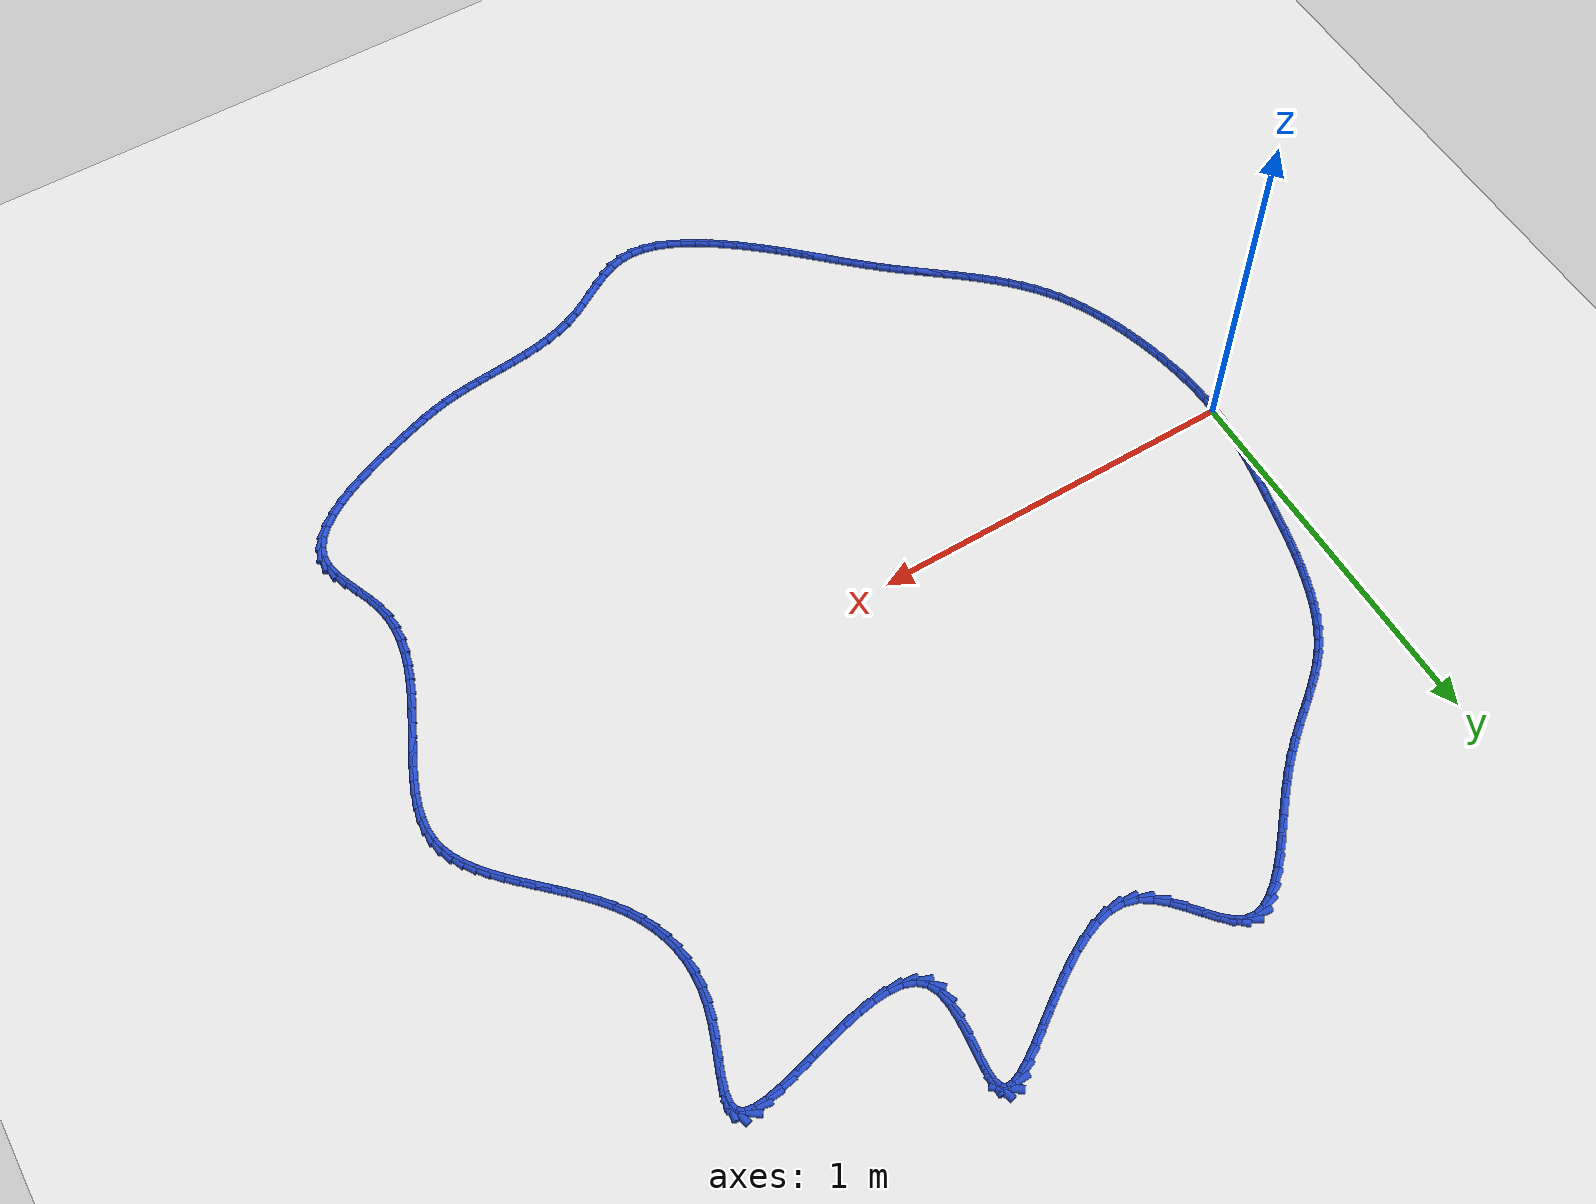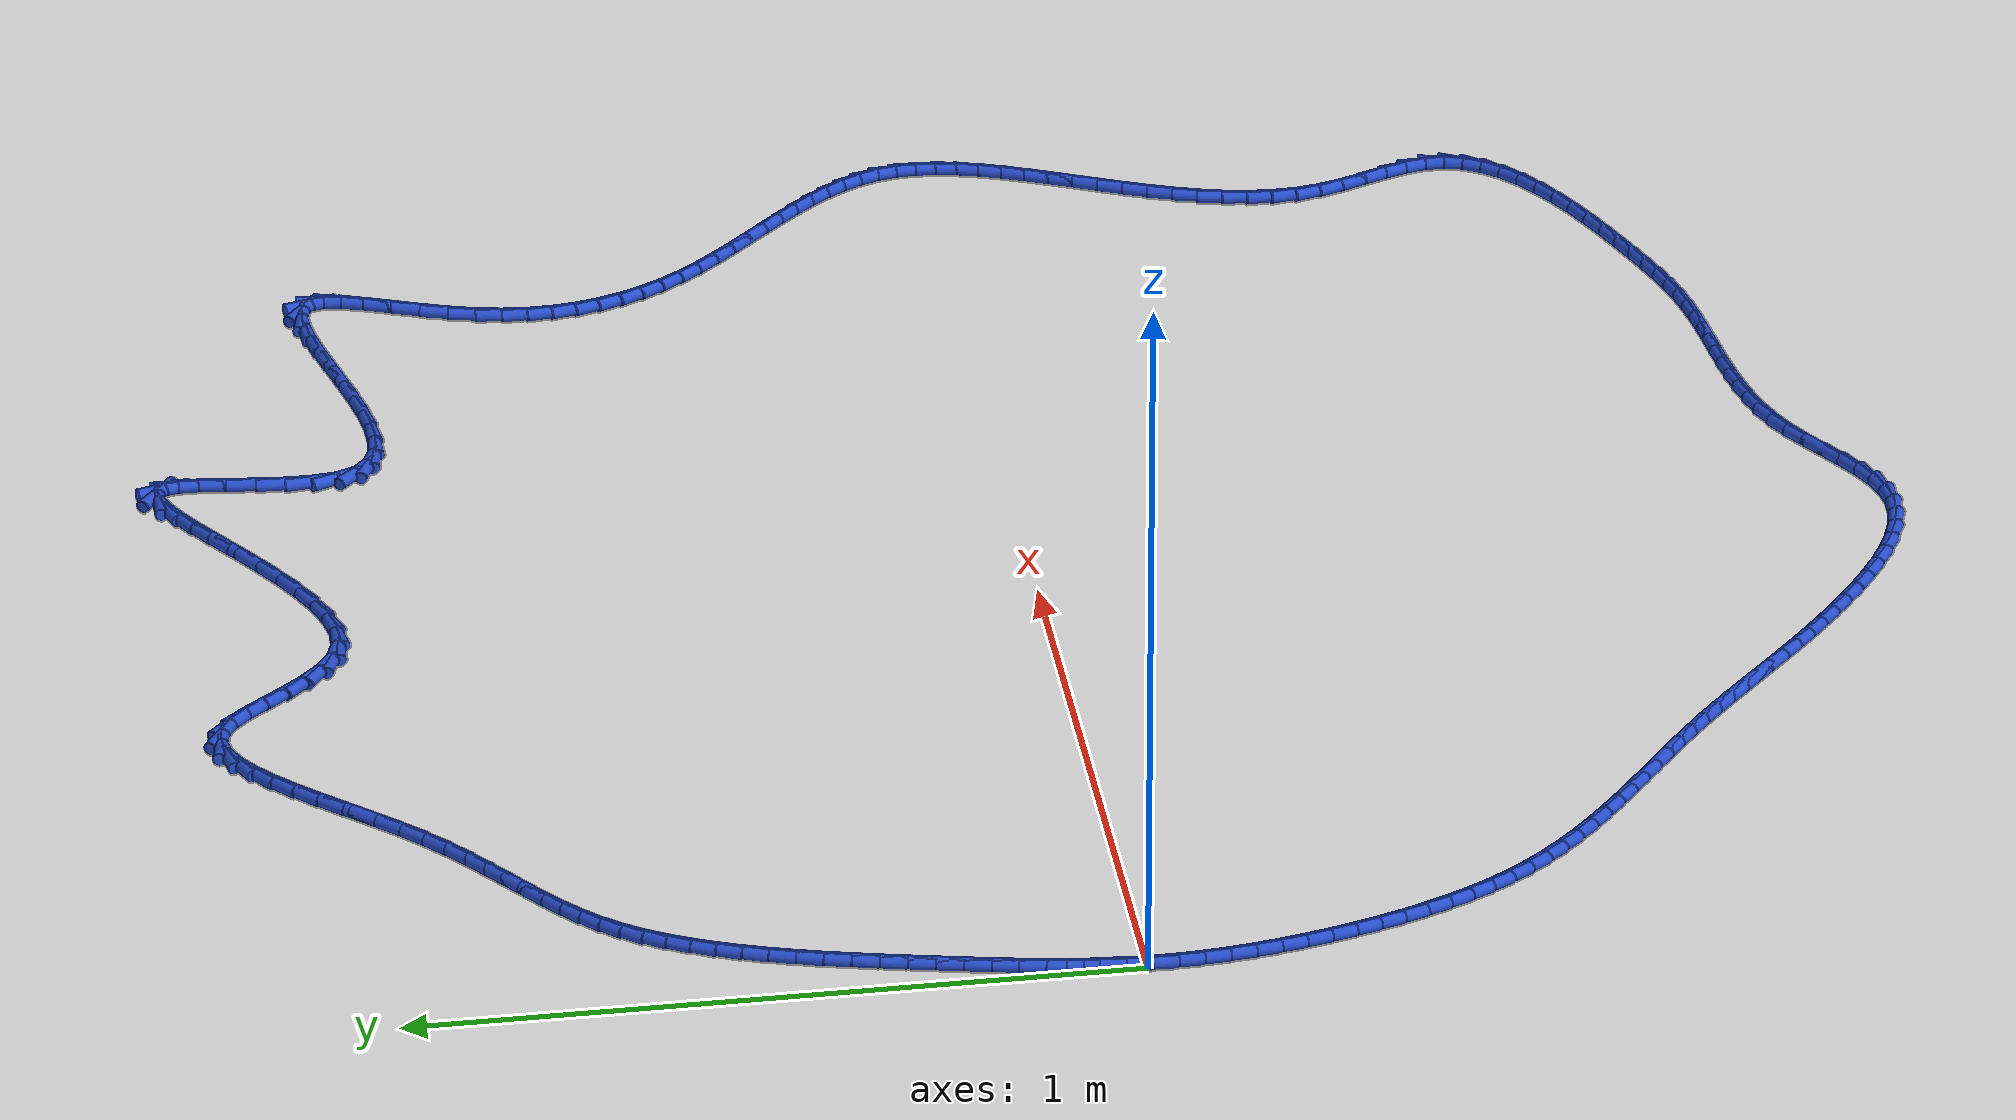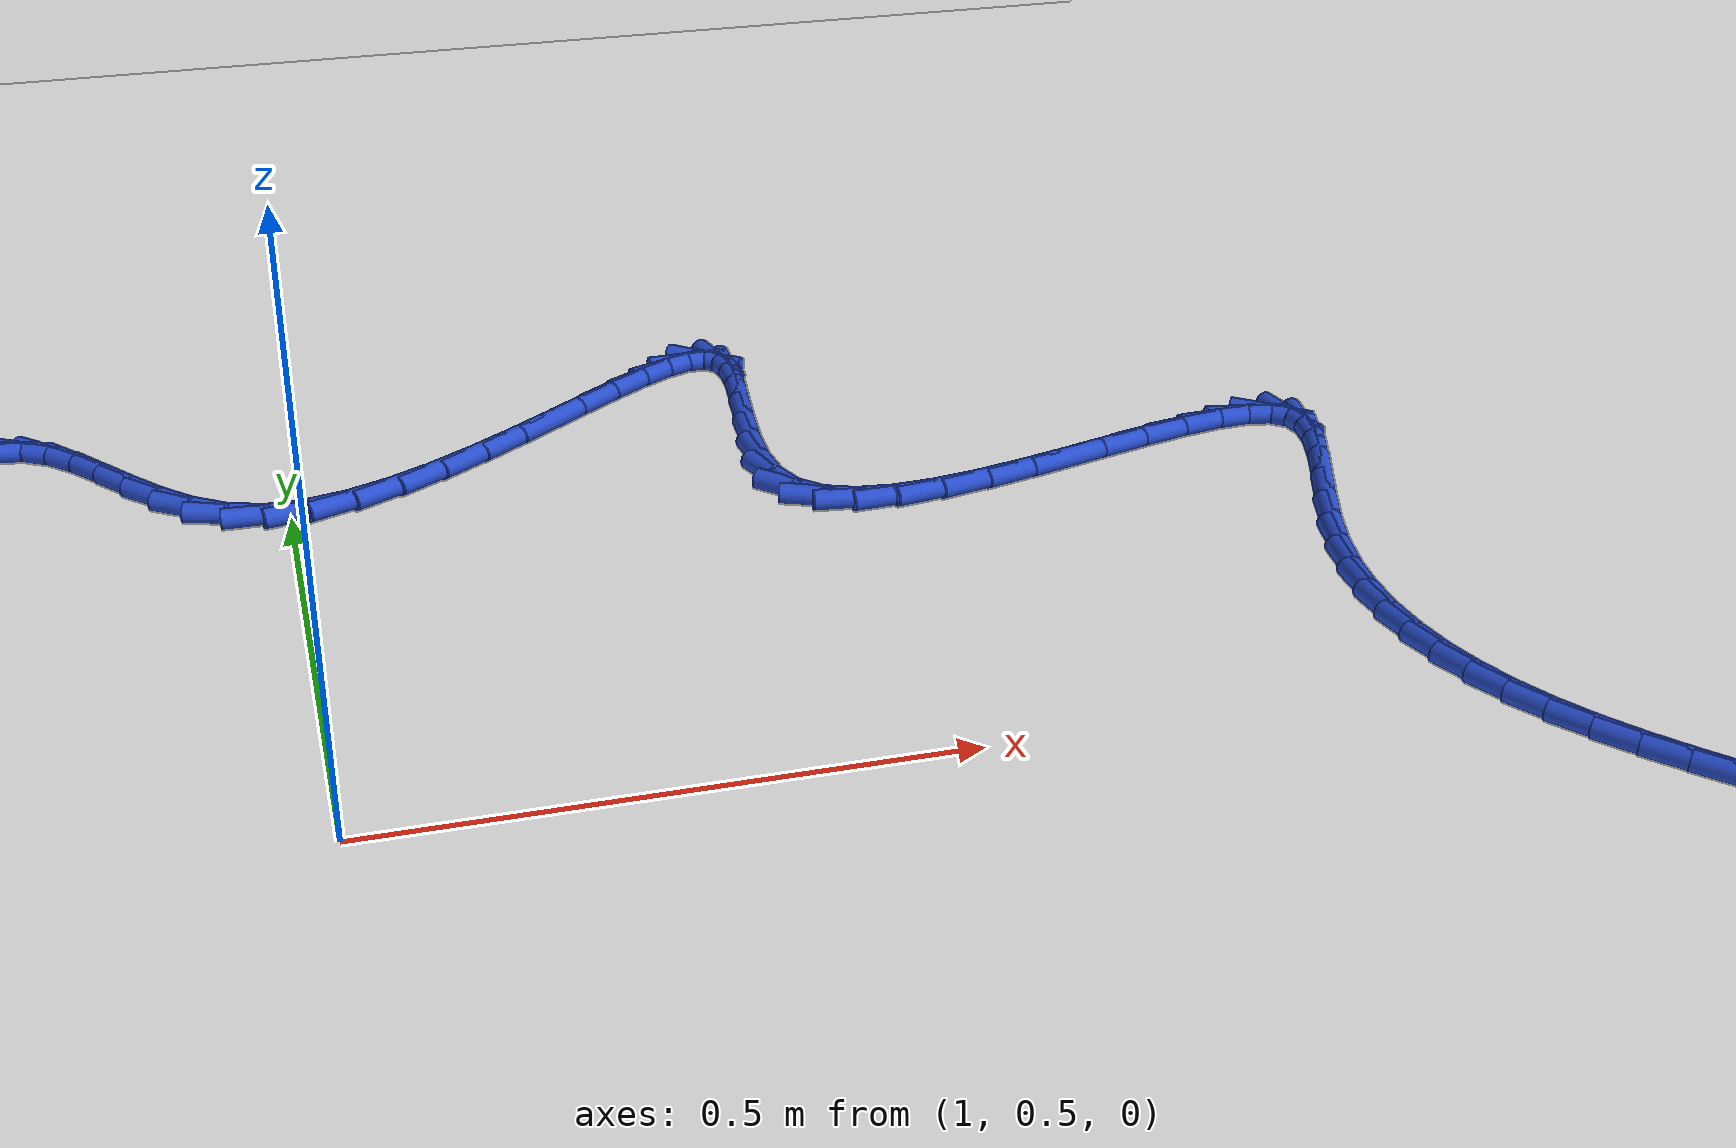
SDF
<sdf version="1.6">
 <world name="default">
  <light name="sun" type="directional">
   <pose>0 0 10 0 -0 0</pose>
   <diffuse>0.8 0.8 0.8 1</diffuse>
   <specular>0.2 0.2 0.2 1</specular>
   <attenuation>
    <range>1000</range>
    <constant>0.9</constant>
    <linear>0.01</linear>
    <quadratic>0.001</quadratic>
   </attenuation>
   <direction>-0.5 0.1 -0.9</direction>
  </light>
  <model name="ground_plane">
   <static>1</static>
   <link name="link">
    <collision name="collision">
     <geometry><plane><normal>0 0 1</normal><size>100 100</size></plane></geometry>
     <surface><friction><ode><mu>100</mu><mu2>50</mu2></ode></friction></surface>
    </collision>
    <visual name="visual">
     <cast_shadows>0</cast_shadows>
     <geometry><plane><normal>0 0 1</normal><size>100 100</size></plane></geometry>
     <material>
      <script><uri>file://media/materials/scripts/gazebo.material</uri><name>Gazebo/WhiteGlow</name></script>
     </material>
    </visual>
   </link>
  </model>
  <gravity>0 0 -9.8</gravity>
  <magnetic_field>6e-06 2.3e-05 -4.2e-05</magnetic_field>
  <atmosphere type="adiabatic"/>
  <physics name="default_physics" default="0" type="ode">
   <max_step_size>0.001</max_step_size>
   <real_time_factor>1</real_time_factor>
   <real_time_update_rate>1000</real_time_update_rate>
  </physics>
  <scene><ambient>0.4 0.4 0.4 1</ambient><background>0.7 0.7 0.7 1</background><shadows>1</shadows></scene>
  <spherical_coordinates>
   <surface_model>EARTH_WGS84</surface_model>
   <latitude_deg>0</latitude_deg>
   <longitude_deg>0</longitude_deg>
   <elevation>0</elevation>
   <heading_deg>0</heading_deg>
  </spherical_coordinates>
  <model name="line">
   <link name="link_0">
    <pose>-5.204170427930421e-18 0.0 0.01 0 1.57 1.5325599736062685</pose>
    <collision name="collision">
     <geometry><cylinder><radius>0.01</radius><length>0.08</length></cylinder></geometry>
    </collision>
    <visual name="visual">
     <material>
      <script><name>Gazebo/Blue</name><uri>file://media/materials/scripts/gazebo.material</uri></script>
     </material>
     <geometry><cylinder><radius>0.01</radius><length>0.08</length></cylinder></geometry>
    </visual>
   </link>
   <link name="link_1">
    <pose>0.0013446943281101467 0.03515081406546295 0.01 0 1.57 1.4915713951892622</pose>
    <collision name="collision">
     <geometry><cylinder><radius>0.01</radius><length>0.08</length></cylinder></geometry>
    </collision>
    <visual name="visual">
     <material>
      <script><name>Gazebo/Blue</name><uri>file://media/materials/scripts/gazebo.material</uri></script>
     </material>
     <geometry><cylinder><radius>0.01</radius><length>0.08</length></cylinder></geometry>
    </visual>
   </link>
   <link name="link_2">
    <pose>0.004127677133646851 0.07020490328031338 0.01 0 1.57 1.456068017332591</pose>
    <collision name="collision">
     <geometry><cylinder><radius>0.01</radius><length>0.08</length></cylinder></geometry>
    </collision>
    <visual name="visual">
     <material>
      <script><name>Gazebo/Blue</name><uri>file://media/materials/scripts/gazebo.material</uri></script>
     </material>
     <geometry><cylinder><radius>0.01</radius><length>0.08</length></cylinder></geometry>
    </visual>
   </link>
   <link name="link_3">
    <pose>0.008164520072093059 0.10523649777379368 0.01 0 1.57 1.4262641740471038</pose>
    <collision name="collision">
     <geometry><cylinder><radius>0.01</radius><length>0.08</length></cylinder></geometry>
    </collision>
    <visual name="visual">
     <material>
      <script><name>Gazebo/Blue</name><uri>file://media/materials/scripts/gazebo.material</uri></script>
     </material>
     <geometry><cylinder><radius>0.01</radius><length>0.08</length></cylinder></geometry>
    </visual>
   </link>
   <link name="link_4">
    <pose>0.013270794798931737 0.14031982767514628 0.01 0 1.57 1.402248888660779</pose>
    <collision name="collision">
     <geometry><cylinder><radius>0.01</radius><length>0.08</length></cylinder></geometry>
    </collision>
    <visual name="visual">
     <material>
      <script><name>Gazebo/Blue</name><uri>file://media/materials/scripts/gazebo.material</uri></script>
     </material>
     <geometry><cylinder><radius>0.01</radius><length>0.08</length></cylinder></geometry>
    </visual>
   </link>
   <link name="link_5">
    <pose>0.019262072969645855 0.17552912311361354 0.01 0 1.57 1.3840144539972912</pose>
    <collision name="collision">
     <geometry><cylinder><radius>0.01</radius><length>0.08</length></cylinder></geometry>
    </collision>
    <visual name="visual">
     <material>
      <script><name>Gazebo/Blue</name><uri>file://media/materials/scripts/gazebo.material</uri></script>
     </material>
     <geometry><cylinder><radius>0.01</radius><length>0.08</length></cylinder></geometry>
    </visual>
   </link>
   <link name="link_6">
    <pose>0.02595392623971837 0.21093861421843793 0.01 0 1.57 1.3714825025432658</pose>
    <collision name="collision">
     <geometry><cylinder><radius>0.01</radius><length>0.08</length></cylinder></geometry>
    </collision>
    <visual name="visual">
     <material>
      <script><name>Gazebo/Blue</name><uri>file://media/materials/scripts/gazebo.material</uri></script>
     </material>
     <geometry><cylinder><radius>0.01</radius><length>0.08</length></cylinder></geometry>
    </visual>
   </link>
   <link name="link_7">
    <pose>0.03316192626463223 0.24662253111886168 0.01 0 1.57 1.3645251251879127</pose>
    <collision name="collision">
     <geometry><cylinder><radius>0.01</radius><length>0.08</length></cylinder></geometry>
    </collision>
    <visual name="visual">
     <material>
      <script><name>Gazebo/Blue</name><uri>file://media/materials/scripts/gazebo.material</uri></script>
     </material>
     <geometry><cylinder><radius>0.01</radius><length>0.08</length></cylinder></geometry>
    </visual>
   </link>
   <link name="link_8">
    <pose>0.04070164559634579 0.28265510317550424 0.01 0 1.57 1.3611633497001698</pose>
    <collision name="collision">
     <geometry><cylinder><radius>0.01</radius><length>0.08</length></cylinder></geometry>
    </collision>
    <visual name="visual">
     <material>
      <script><name>Gazebo/Blue</name><uri>file://media/materials/scripts/gazebo.material</uri></script>
     </material>
     <geometry><cylinder><radius>0.01</radius><length>0.08</length></cylinder></geometry>
    </visual>
   </link>
   <link name="link_9">
    <pose>0.04844718711913222 0.319060376816062 0.01 0 1.57 1.3545885935136082</pose>
    <collision name="collision">
     <geometry><cylinder><radius>0.01</radius><length>0.08</length></cylinder></geometry>
    </collision>
    <visual name="visual">
     <material>
      <script><name>Gazebo/Blue</name><uri>file://media/materials/scripts/gazebo.material</uri></script>
     </material>
     <geometry><cylinder><radius>0.01</radius><length>0.08</length></cylinder></geometry>
    </visual>
   </link>
   <link name="link_10">
    <pose>0.056489567014441376 0.355676420616888 0.01 0 1.57 1.343238359815529</pose>
    <collision name="collision">
     <geometry><cylinder><radius>0.01</radius><length>0.08</length></cylinder></geometry>
    </collision>
    <visual name="visual">
     <material>
      <script><name>Gazebo/Blue</name><uri>file://media/materials/scripts/gazebo.material</uri></script>
     </material>
     <geometry><cylinder><radius>0.01</radius><length>0.08</length></cylinder></geometry>
    </visual>
   </link>
   <link name="link_11">
    <pose>0.06497003967180633 0.3922982297507394 0.01 0 1.57 1.327002091465118</pose>
    <collision name="collision">
     <geometry><cylinder><radius>0.01</radius><length>0.08</length></cylinder></geometry>
    </collision>
    <visual name="visual">
     <material>
      <script><name>Gazebo/Blue</name><uri>file://media/materials/scripts/gazebo.material</uri></script>
     </material>
     <geometry><cylinder><radius>0.01</radius><length>0.08</length></cylinder></geometry>
    </visual>
   </link>
   <link name="link_12">
    <pose>0.07402985948076006 0.42872079939037333 0.01 0 1.57 1.3056495504041556</pose>
    <collision name="collision">
     <geometry><cylinder><radius>0.01</radius><length>0.08</length></cylinder></geometry>
    </collision>
    <visual name="visual">
     <material>
      <script><name>Gazebo/Blue</name><uri>file://media/materials/scripts/gazebo.material</uri></script>
     </material>
     <geometry><cylinder><radius>0.01</radius><length>0.08</length></cylinder></geometry>
    </visual>
   </link>
   <link name="link_13">
    <pose>0.08381028083083567 0.464739124708547 0.01 0 1.57 1.2788329640013834</pose>
    <collision name="collision">
     <geometry><cylinder><radius>0.01</radius><length>0.08</length></cylinder></geometry>
    </collision>
    <visual name="visual">
     <material>
      <script><name>Gazebo/Blue</name><uri>file://media/materials/scripts/gazebo.material</uri></script>
     </material>
     <geometry><cylinder><radius>0.01</radius><length>0.08</length></cylinder></geometry>
    </visual>
   </link>
   <link name="link_14">
    <pose>0.09445255811156615 0.5001482008780173 0.01 0 1.57 1.2460886551369075</pose>
    <collision name="collision">
     <geometry><cylinder><radius>0.01</radius><length>0.08</length></cylinder></geometry>
    </collision>
    <visual name="visual">
     <material>
      <script><name>Gazebo/Blue</name><uri>file://media/materials/scripts/gazebo.material</uri></script>
     </material>
     <geometry><cylinder><radius>0.01</radius><length>0.08</length></cylinder></geometry>
    </visual>
   </link>
   <link name="link_15">
    <pose>0.10609794571248463 0.5347430230715414 0.01 0 1.57 1.2068417800955957</pose>
    <collision name="collision">
     <geometry><cylinder><radius>0.01</radius><length>0.08</length></cylinder></geometry>
    </collision>
    <visual name="visual">
     <material>
      <script><name>Gazebo/Blue</name><uri>file://media/materials/scripts/gazebo.material</uri></script>
     </material>
     <geometry><cylinder><radius>0.01</radius><length>0.08</length></cylinder></geometry>
    </visual>
   </link>
   <link name="link_16">
    <pose>0.11888769802312407 0.5683185864618768 0.01 0 1.57 1.160419736200274</pose>
    <collision name="collision">
     <geometry><cylinder><radius>0.01</radius><length>0.08</length></cylinder></geometry>
    </collision>
    <visual name="visual">
     <material>
      <script><name>Gazebo/Blue</name><uri>file://media/materials/scripts/gazebo.material</uri></script>
     </material>
     <geometry><cylinder><radius>0.01</radius><length>0.08</length></cylinder></geometry>
    </visual>
   </link>
   <link name="link_17">
    <pose>0.13296306943301756 0.6006698862217801 0.01 0 1.57 1.1060826234121506</pose>
    <collision name="collision">
     <geometry><cylinder><radius>0.01</radius><length>0.08</length></cylinder></geometry>
    </collision>
    <visual name="visual">
     <material>
      <script><name>Gazebo/Blue</name><uri>file://media/materials/scripts/gazebo.material</uri></script>
     </material>
     <geometry><cylinder><radius>0.01</radius><length>0.08</length></cylinder></geometry>
    </visual>
   </link>
   <link name="link_18">
    <pose>0.1484653143316981 0.6315919175240087 0.01 0 1.57 1.0430824991105236</pose>
    <collision name="collision">
     <geometry><cylinder><radius>0.01</radius><length>0.08</length></cylinder></geometry>
    </collision>
    <visual name="visual">
     <material>
      <script><name>Gazebo/Blue</name><uri>file://media/materials/scripts/gazebo.material</uri></script>
     </material>
     <geometry><cylinder><radius>0.01</radius><length>0.08</length></cylinder></geometry>
    </visual>
   </link>
   <link name="link_19">
    <pose>0.1655356871086988 0.6608796755413195 0.01 0 1.57 0.9707655645267002</pose>
    <collision name="collision">
     <geometry><cylinder><radius>0.01</radius><length>0.08</length></cylinder></geometry>
    </collision>
    <visual name="visual">
     <material>
      <script><name>Gazebo/Blue</name><uri>file://media/materials/scripts/gazebo.material</uri></script>
     </material>
     <geometry><cylinder><radius>0.01</radius><length>0.08</length></cylinder></geometry>
    </visual>
   </link>
   <link name="link_20">
    <pose>0.18431544215355264 0.6883281554464699 0.01 0 1.57 0.8892927408092125</pose>
    <collision name="collision">
     <geometry><cylinder><radius>0.01</radius><length>0.08</length></cylinder></geometry>
    </collision>
    <visual name="visual">
     <material>
      <script><name>Gazebo/Blue</name><uri>file://media/materials/scripts/gazebo.material</uri></script>
     </material>
     <geometry><cylinder><radius>0.01</radius><length>0.08</length></cylinder></geometry>
    </visual>
   </link>
   <link name="link_21">
    <pose>0.20493725586857156 0.7137510517195338 0.01 0 1.57 0.8103554758994558</pose>
    <collision name="collision">
     <geometry><cylinder><radius>0.01</radius><length>0.08</length></cylinder></geometry>
    </collision>
    <visual name="visual">
     <material>
      <script><name>Gazebo/Blue</name><uri>file://media/materials/scripts/gazebo.material</uri></script>
     </material>
     <geometry><cylinder><radius>0.01</radius><length>0.08</length></cylinder></geometry>
    </visual>
   </link>
   <link name="link_22">
    <pose>0.22736588889798603 0.737328101396127 0.01 0 1.57 0.7464784395150182</pose>
    <collision name="collision">
     <geometry><cylinder><radius>0.01</radius><length>0.08</length></cylinder></geometry>
    </collision>
    <visual name="visual">
     <material>
      <script><name>Gazebo/Blue</name><uri>file://media/materials/scripts/gazebo.material</uri></script>
     </material>
     <geometry><cylinder><radius>0.01</radius><length>0.08</length></cylinder></geometry>
    </visual>
   </link>
   <link name="link_23">
    <pose>0.2514130473942208 0.759572687728024 0.01 0 1.57 0.6996120722404389</pose>
    <collision name="collision">
     <geometry><cylinder><radius>0.01</radius><length>0.08</length></cylinder></geometry>
    </collision>
    <visual name="visual">
     <material>
      <script><name>Gazebo/Blue</name><uri>file://media/materials/scripts/gazebo.material</uri></script>
     </material>
     <geometry><cylinder><radius>0.01</radius><length>0.08</length></cylinder></geometry>
    </visual>
   </link>
   <link name="link_24">
    <pose>0.27688483977929285 0.7810103965593411 0.01 0 1.57 0.6700281288413371</pose>
    <collision name="collision">
     <geometry><cylinder><radius>0.01</radius><length>0.08</length></cylinder></geometry>
    </collision>
    <visual name="visual">
     <material>
      <script><name>Gazebo/Blue</name><uri>file://media/materials/scripts/gazebo.material</uri></script>
     </material>
     <geometry><cylinder><radius>0.01</radius><length>0.08</length></cylinder></geometry>
    </visual>
   </link>
   <link name="link_25">
    <pose>0.30358737447521916 0.8021668137341953 0.01 0 1.57 0.6571146407556601</pose>
    <collision name="collision">
     <geometry><cylinder><radius>0.01</radius><length>0.08</length></cylinder></geometry>
    </collision>
    <visual name="visual">
     <material>
      <script><name>Gazebo/Blue</name><uri>file://media/materials/scripts/gazebo.material</uri></script>
     </material>
     <geometry><cylinder><radius>0.01</radius><length>0.08</length></cylinder></geometry>
    </visual>
   </link>
   <link name="link_26">
    <pose>0.33132675990401705 0.8235675250967033 0.01 0 1.57 0.6597312314286204</pose>
    <collision name="collision">
     <geometry><cylinder><radius>0.01</radius><length>0.08</length></cylinder></geometry>
    </collision>
    <visual name="visual">
     <material>
      <script><name>Gazebo/Blue</name><uri>file://media/materials/scripts/gazebo.material</uri></script>
     </material>
     <geometry><cylinder><radius>0.01</radius><length>0.08</length></cylinder></geometry>
    </visual>
   </link>
   <link name="link_27">
    <pose>0.3599091044877033 0.8457381164909813 0.01 0 1.57 0.6764267815310502</pose>
    <collision name="collision">
     <geometry><cylinder><radius>0.01</radius><length>0.08</length></cylinder></geometry>
    </collision>
    <visual name="visual">
     <material>
      <script><name>Gazebo/Blue</name><uri>file://media/materials/scripts/gazebo.material</uri></script>
     </material>
     <geometry><cylinder><radius>0.01</radius><length>0.08</length></cylinder></geometry>
    </visual>
   </link>
   <link name="link_28">
    <pose>0.38914051664829513 0.869204173761146 0.01 0 1.57 0.7055395580989225</pose>
    <collision name="collision">
     <geometry><cylinder><radius>0.01</radius><length>0.08</length></cylinder></geometry>
    </collision>
    <visual name="visual">
     <material>
      <script><name>Gazebo/Blue</name><uri>file://media/materials/scripts/gazebo.material</uri></script>
     </material>
     <geometry><cylinder><radius>0.01</radius><length>0.08</length></cylinder></geometry>
    </visual>
   </link>
   <link name="link_29">
    <pose>0.41882710480780966 0.8944912827513144 0.01 0 1.57 0.7452311552635893</pose>
    <collision name="collision">
     <geometry><cylinder><radius>0.01</radius><length>0.08</length></cylinder></geometry>
    </collision>
    <visual name="visual">
     <material>
      <script><name>Gazebo/Blue</name><uri>file://media/materials/scripts/gazebo.material</uri></script>
     </material>
     <geometry><cylinder><radius>0.01</radius><length>0.08</length></cylinder></geometry>
    </visual>
   </link>
   <link name="link_30">
    <pose>0.4487749773882638 0.9221250293056027 0.01 0 1.57 0.7922068542492547</pose>
    <collision name="collision">
     <geometry><cylinder><radius>0.01</radius><length>0.08</length></cylinder></geometry>
    </collision>
    <visual name="visual">
     <material>
      <script><name>Gazebo/Blue</name><uri>file://media/materials/scripts/gazebo.material</uri></script>
     </material>
     <geometry><cylinder><radius>0.01</radius><length>0.08</length></cylinder></geometry>
    </visual>
   </link>
   <link name="link_31">
    <pose>0.4787946413078842 0.9525562912514908 0.01 0 1.57 0.8289208667558533</pose>
    <collision name="collision">
     <geometry><cylinder><radius>0.01</radius><length>0.08</length></cylinder></geometry>
    </collision>
    <visual name="visual">
     <material>
      <script><name>Gazebo/Blue</name><uri>file://media/materials/scripts/gazebo.material</uri></script>
     </material>
     <geometry><cylinder><radius>0.01</radius><length>0.08</length></cylinder></geometry>
    </visual>
   </link>
   <link name="link_32">
    <pose>0.5087549478012293 0.9852449740596831 0.01 0 1.57 0.8466002324156454</pose>
    <collision name="collision">
     <geometry><cylinder><radius>0.01</radius><length>0.08</length></cylinder></geometry>
    </collision>
    <visual name="visual">
     <material>
      <script><name>Gazebo/Blue</name><uri>file://media/materials/scripts/gazebo.material</uri></script>
     </material>
     <geometry><cylinder><radius>0.01</radius><length>0.08</length></cylinder></geometry>
    </visual>
   </link>
   <link name="link_33">
    <pose>0.5385661235797489 1.0189482248788024 0.01 0 1.57 0.8469844092881079</pose>
    <collision name="collision">
     <geometry><cylinder><radius>0.01</radius><length>0.08</length></cylinder></geometry>
    </collision>
    <visual name="visual">
     <material>
      <script><name>Gazebo/Blue</name><uri>file://media/materials/scripts/gazebo.material</uri></script>
     </material>
     <geometry><cylinder><radius>0.01</radius><length>0.08</length></cylinder></geometry>
    </visual>
   </link>
   <link name="link_34">
    <pose>0.5681392739268819 1.052408268400419 0.01 0 1.57 0.82969263930275</pose>
    <collision name="collision">
     <geometry><cylinder><radius>0.01</radius><length>0.08</length></cylinder></geometry>
    </collision>
    <visual name="visual">
     <material>
      <script><name>Gazebo/Blue</name><uri>file://media/materials/scripts/gazebo.material</uri></script>
     </material>
     <geometry><cylinder><radius>0.01</radius><length>0.08</length></cylinder></geometry>
    </visual>
   </link>
   <link name="link_35">
    <pose>0.5973855041260675 1.0843673293161042 0.01 0 1.57 0.7917720748038594</pose>
    <collision name="collision">
     <geometry><cylinder><radius>0.01</radius><length>0.08</length></cylinder></geometry>
    </collision>
    <visual name="visual">
     <material>
      <script><name>Gazebo/Blue</name><uri>file://media/materials/scripts/gazebo.material</uri></script>
     </material>
     <geometry><cylinder><radius>0.01</radius><length>0.08</length></cylinder></geometry>
    </visual>
   </link>
   <link name="link_36">
    <pose>0.6262159194607443 1.1135676323174295 0.01 0 1.57 0.7267481290648145</pose>
    <collision name="collision">
     <geometry><cylinder><radius>0.01</radius><length>0.08</length></cylinder></geometry>
    </collision>
    <visual name="visual">
     <material>
      <script><name>Gazebo/Blue</name><uri>file://media/materials/scripts/gazebo.material</uri></script>
     </material>
     <geometry><cylinder><radius>0.01</radius><length>0.08</length></cylinder></geometry>
    </visual>
   </link>
   <link name="link_37">
    <pose>0.6545416252143513 1.138751402095965 0.01 0 1.57 0.6226525753252955</pose>
    <collision name="collision">
     <geometry><cylinder><radius>0.01</radius><length>0.08</length></cylinder></geometry>
    </collision>
    <visual name="visual">
     <material>
      <script><name>Gazebo/Blue</name><uri>file://media/materials/scripts/gazebo.material</uri></script>
     </material>
     <geometry><cylinder><radius>0.01</radius><length>0.08</length></cylinder></geometry>
    </visual>
   </link>
   <link name="link_38">
    <pose>0.682273726670328 1.1586608633432824 0.01 0 1.57 0.45927800787577494</pose>
    <collision name="collision">
     <geometry><cylinder><radius>0.01</radius><length>0.08</length></cylinder></geometry>
    </collision>
    <visual name="visual">
     <material>
      <script><name>Gazebo/Blue</name><uri>file://media/materials/scripts/gazebo.material</uri></script>
     </material>
     <geometry><cylinder><radius>0.01</radius><length>0.08</length></cylinder></geometry>
    </visual>
   </link>
   <link name="link_39">
    <pose>0.7093233291121132 1.1720382407509526 0.01 0 1.57 0.20950914462414016</pose>
    <collision name="collision">
     <geometry><cylinder><radius>0.01</radius><length>0.08</length></cylinder></geometry>
    </collision>
    <visual name="visual">
     <material>
      <script><name>Gazebo/Blue</name><uri>file://media/materials/scripts/gazebo.material</uri></script>
     </material>
     <geometry><cylinder><radius>0.01</radius><length>0.08</length></cylinder></geometry>
    </visual>
   </link>
   <link name="link_40">
    <pose>0.7356015378231455 1.1776257590105468 0.01 0 1.57 -0.13529735880801397</pose>
    <collision name="collision">
     <geometry><cylinder><radius>0.01</radius><length>0.08</length></cylinder></geometry>
    </collision>
    <visual name="visual">
     <material>
      <script><name>Gazebo/Blue</name><uri>file://media/materials/scripts/gazebo.material</uri></script>
     </material>
     <geometry><cylinder><radius>0.01</radius><length>0.08</length></cylinder></geometry>
    </visual>
   </link>
   <link name="link_41">
    <pose>0.7610194580868641 1.1741656428136353 0.01 0 1.57 -0.5036402263211666</pose>
    <collision name="collision">
     <geometry><cylinder><radius>0.01</radius><length>0.08</length></cylinder></geometry>
    </collision>
    <visual name="visual">
     <material>
      <script><name>Gazebo/Blue</name><uri>file://media/materials/scripts/gazebo.material</uri></script>
     </material>
     <geometry><cylinder><radius>0.01</radius><length>0.08</length></cylinder></geometry>
    </visual>
   </link>
   <link name="link_42">
    <pose>0.7855310765392158 1.1606587956814365 0.01 0 1.57 -0.7426309171887576</pose>
    <collision name="collision">
     <geometry><cylinder><radius>0.01</radius><length>0.08</length></cylinder></geometry>
    </collision>
    <visual name="visual">
     <material>
      <script><name>Gazebo/Blue</name><uri>file://media/materials/scripts/gazebo.material</uri></script>
     </material>
     <geometry><cylinder><radius>0.01</radius><length>0.08</length></cylinder></geometry>
    </visual>
   </link>
   <link name="link_43">
    <pose>0.8095115075055871 1.1386465451531964 0.01 0 1.57 -0.8525757150796696</pose>
    <collision name="collision">
     <geometry><cylinder><radius>0.01</radius><length>0.08</length></cylinder></geometry>
    </collision>
    <visual name="visual">
     <material>
      <script><name>Gazebo/Blue</name><uri>file://media/materials/scripts/gazebo.material</uri></script>
     </material>
     <geometry><cylinder><radius>0.01</radius><length>0.08</length></cylinder></geometry>
    </visual>
   </link>
   <link name="link_44">
    <pose>0.8335748311029957 1.1111117635817012 0.01 0 1.57 -0.8816843196345426</pose>
    <collision name="collision">
     <geometry><cylinder><radius>0.01</radius><length>0.08</length></cylinder></geometry>
    </collision>
    <visual name="visual">
     <material>
      <script><name>Gazebo/Blue</name><uri>file://media/materials/scripts/gazebo.material</uri></script>
     </material>
     <geometry><cylinder><radius>0.01</radius><length>0.08</length></cylinder></geometry>
    </visual>
   </link>
   <link name="link_45">
    <pose>0.8583378680032573 1.0810538555293325 0.01 0 1.57 -0.8482327573708495</pose>
    <collision name="collision">
     <geometry><cylinder><radius>0.01</radius><length>0.08</length></cylinder></geometry>
    </collision>
    <visual name="visual">
     <material>
      <script><name>Gazebo/Blue</name><uri>file://media/materials/scripts/gazebo.material</uri></script>
     </material>
     <geometry><cylinder><radius>0.01</radius><length>0.08</length></cylinder></geometry>
    </visual>
   </link>
   <link name="link_46">
    <pose>0.8844174388781867 1.0514722255584716 0.01 0 1.57 -0.7501758938900057</pose>
    <collision name="collision">
     <geometry><cylinder><radius>0.01</radius><length>0.08</length></cylinder></geometry>
    </collision>
    <visual name="visual">
     <material>
      <script><name>Gazebo/Blue</name><uri>file://media/materials/scripts/gazebo.material</uri></script>
     </material>
     <geometry><cylinder><radius>0.01</radius><length>0.08</length></cylinder></geometry>
    </visual>
   </link>
   <link name="link_47">
    <pose>0.9124303643995991 1.0253662782315007 0.01 0 1.57 -0.5709473359176263</pose>
    <collision name="collision">
     <geometry><cylinder><radius>0.01</radius><length>0.08</length></cylinder></geometry>
    </collision>
    <visual name="visual">
     <material>
      <script><name>Gazebo/Blue</name><uri>file://media/materials/scripts/gazebo.material</uri></script>
     </material>
     <geometry><cylinder><radius>0.01</radius><length>0.08</length></cylinder></geometry>
    </visual>
   </link>
   <link name="link_48">
    <pose>0.9429934652393098 1.005735418110801 0.01 0 1.57 -0.2962546962150804</pose>
    <collision name="collision">
     <geometry><cylinder><radius>0.01</radius><length>0.08</length></cylinder></geometry>
    </collision>
    <visual name="visual">
     <material>
      <script><name>Gazebo/Blue</name><uri>file://media/materials/scripts/gazebo.material</uri></script>
     </material>
     <geometry><cylinder><radius>0.01</radius><length>0.08</length></cylinder></geometry>
    </visual>
   </link>
   <link name="link_49">
    <pose>0.9766861403617633 0.9954511572135784 0.01 0 1.57 -0.010365268480151535</pose>
    <collision name="collision">
     <geometry><cylinder><radius>0.01</radius><length>0.08</length></cylinder></geometry>
    </collision>
    <visual name="visual">
     <material>
      <script><name>Gazebo/Blue</name><uri>file://media/materials/scripts/gazebo.material</uri></script>
     </material>
     <geometry><cylinder><radius>0.01</radius><length>0.08</length></cylinder></geometry>
    </visual>
   </link>
   <link name="link_50">
    <pose>1.0134105531747455 0.9950704851819173 0.01 0 1.57 0.2036394699474693</pose>
    <collision name="collision">
     <geometry><cylinder><radius>0.01</radius><length>0.08</length></cylinder></geometry>
    </collision>
    <visual name="visual">
     <material>
      <script><name>Gazebo/Blue</name><uri>file://media/materials/scripts/gazebo.material</uri></script>
     </material>
     <geometry><cylinder><radius>0.01</radius><length>0.08</length></cylinder></geometry>
    </visual>
   </link>
   <link name="link_51">
    <pose>1.0524801623681805 1.0031384325567623 0.01 0 1.57 0.35291821953378505</pose>
    <collision name="collision">
     <geometry><cylinder><radius>0.01</radius><length>0.08</length></cylinder></geometry>
    </collision>
    <visual name="visual">
     <material>
      <script><name>Gazebo/Blue</name><uri>file://media/materials/scripts/gazebo.material</uri></script>
     </material>
     <geometry><cylinder><radius>0.01</radius><length>0.08</length></cylinder></geometry>
    </visual>
   </link>
   <link name="link_52">
    <pose>1.0931888201002586 1.018133022534349 0.01 0 1.57 0.45551673510175417</pose>
    <collision name="collision">
     <geometry><cylinder><radius>0.01</radius><length>0.08</length></cylinder></geometry>
    </collision>
    <visual name="visual">
     <material>
      <script><name>Gazebo/Blue</name><uri>file://media/materials/scripts/gazebo.material</uri></script>
     </material>
     <geometry><cylinder><radius>0.01</radius><length>0.08</length></cylinder></geometry>
    </visual>
   </link>
   <link name="link_53">
    <pose>1.1348303785291705 1.038532278310914 0.01 0 1.57 0.5255538432778428</pose>
    <collision name="collision">
     <geometry><cylinder><radius>0.01</radius><length>0.08</length></cylinder></geometry>
    </collision>
    <visual name="visual">
     <material>
      <script><name>Gazebo/Blue</name><uri>file://media/materials/scripts/gazebo.material</uri></script>
     </material>
     <geometry><cylinder><radius>0.01</radius><length>0.08</length></cylinder></geometry>
    </visual>
   </link>
   <link name="link_54">
    <pose>1.1766986898131069 1.0628142230826934 0.01 0 1.57 0.5719440878847482</pose>
    <collision name="collision">
     <geometry><cylinder><radius>0.01</radius><length>0.08</length></cylinder></geometry>
    </collision>
    <visual name="visual">
     <material>
      <script><name>Gazebo/Blue</name><uri>file://media/materials/scripts/gazebo.material</uri></script>
     </material>
     <geometry><cylinder><radius>0.01</radius><length>0.08</length></cylinder></geometry>
    </visual>
   </link>
   <link name="link_55">
    <pose>1.2180876061102583 1.089456880045923 0.01 0 1.57 0.5996065504426453</pose>
    <collision name="collision">
     <geometry><cylinder><radius>0.01</radius><length>0.08</length></cylinder></geometry>
    </collision>
    <visual name="visual">
     <material>
      <script><name>Gazebo/Blue</name><uri>file://media/materials/scripts/gazebo.material</uri></script>
     </material>
     <geometry><cylinder><radius>0.01</radius><length>0.08</length></cylinder></geometry>
    </visual>
   </link>
   <link name="link_56">
    <pose>1.2582909795788157 1.116938272396839 0.01 0 1.57 0.6103750464510356</pose>
    <collision name="collision">
     <geometry><cylinder><radius>0.01</radius><length>0.08</length></cylinder></geometry>
    </collision>
    <visual name="visual">
     <material>
      <script><name>Gazebo/Blue</name><uri>file://media/materials/scripts/gazebo.material</uri></script>
     </material>
     <geometry><cylinder><radius>0.01</radius><length>0.08</length></cylinder></geometry>
    </visual>
   </link>
   <link name="link_57">
    <pose>1.29660266237697 1.1437364233316785 0.01 0 1.57 0.6030411211472769</pose>
    <collision name="collision">
     <geometry><cylinder><radius>0.01</radius><length>0.08</length></cylinder></geometry>
    </collision>
    <visual name="visual">
     <material>
      <script><name>Gazebo/Blue</name><uri>file://media/materials/scripts/gazebo.material</uri></script>
     </material>
     <geometry><cylinder><radius>0.01</radius><length>0.08</length></cylinder></geometry>
    </visual>
   </link>
   <link name="link_58">
    <pose>1.332316506662911 1.1683293560466765 0.01 0 1.57 0.5720102565742372</pose>
    <collision name="collision">
     <geometry><cylinder><radius>0.01</radius><length>0.08</length></cylinder></geometry>
    </collision>
    <visual name="visual">
     <material>
      <script><name>Gazebo/Blue</name><uri>file://media/materials/scripts/gazebo.material</uri></script>
     </material>
     <geometry><cylinder><radius>0.01</radius><length>0.08</length></cylinder></geometry>
    </visual>
   </link>
   <link name="link_59">
    <pose>1.3647263645948302 1.1891950937380698 0.01 0 1.57 0.5027544762916225</pose>
    <collision name="collision">
     <geometry><cylinder><radius>0.01</radius><length>0.08</length></cylinder></geometry>
    </collision>
    <visual name="visual">
     <material>
      <script><name>Gazebo/Blue</name><uri>file://media/materials/scripts/gazebo.material</uri></script>
     </material>
     <geometry><cylinder><radius>0.01</radius><length>0.08</length></cylinder></geometry>
    </visual>
   </link>
   <link name="link_60">
    <pose>1.3931260883309178 1.2048116596020941 0.01 0 1.57 0.35744204974219007</pose>
    <collision name="collision">
     <geometry><cylinder><radius>0.01</radius><length>0.08</length></cylinder></geometry>
    </collision>
    <visual name="visual">
     <material>
      <script><name>Gazebo/Blue</name><uri>file://media/materials/scripts/gazebo.material</uri></script>
     </material>
     <geometry><cylinder><radius>0.01</radius><length>0.08</length></cylinder></geometry>
    </visual>
   </link>
   <link name="link_61">
    <pose>1.4168095300293657 1.2136570768349864 0.01 0 1.57 0.030235098615312313</pose>
    <collision name="collision">
     <geometry><cylinder><radius>0.01</radius><length>0.08</length></cylinder></geometry>
    </collision>
    <visual name="visual">
     <material>
      <script><name>Gazebo/Blue</name><uri>file://media/materials/scripts/gazebo.material</uri></script>
     </material>
     <geometry><cylinder><radius>0.01</radius><length>0.08</length></cylinder></geometry>
    </visual>
   </link>
   <link name="link_62">
    <pose>1.4350705418483627 1.214209368632982 0.01 0 1.57 -0.6520694940871782</pose>
    <collision name="collision">
     <geometry><cylinder><radius>0.01</radius><length>0.08</length></cylinder></geometry>
    </collision>
    <visual name="visual">
     <material>
      <script><name>Gazebo/Blue</name><uri>file://media/materials/scripts/gazebo.material</uri></script>
     </material>
     <geometry><cylinder><radius>0.01</radius><length>0.08</length></cylinder></geometry>
    </visual>
   </link>
   <link name="link_63">
    <pose>1.4472029759461014 1.2049465581923178 0.01 0 1.57 -1.3096282143864442</pose>
    <collision name="collision">
     <geometry><cylinder><radius>0.01</radius><length>0.08</length></cylinder></geometry>
    </collision>
    <visual name="visual">
     <material>
      <script><name>Gazebo/Blue</name><uri>file://media/materials/scripts/gazebo.material</uri></script>
     </material>
     <geometry><cylinder><radius>0.01</radius><length>0.08</length></cylinder></geometry>
    </visual>
   </link>
   <link name="link_64">
    <pose>1.452648510428562 1.184572107967339 0.01 0 1.57 1.5665216712756018</pose>
    <collision name="collision">
     <geometry><cylinder><radius>0.01</radius><length>0.08</length></cylinder></geometry>
    </collision>
    <visual name="visual">
     <material>
      <script><name>Gazebo/Blue</name><uri>file://media/materials/scripts/gazebo.material</uri></script>
     </material>
     <geometry><cylinder><radius>0.01</radius><length>0.08</length></cylinder></geometry>
    </visual>
   </link>
   <link name="link_65">
    <pose>1.45251926478421 1.1543369564922674 0.01 0 1.57 1.476101667094157</pose>
    <collision name="collision">
     <geometry><cylinder><radius>0.01</radius><length>0.08</length></cylinder></geometry>
    </collision>
    <visual name="visual">
     <material>
      <script><name>Gazebo/Blue</name><uri>file://media/materials/scripts/gazebo.material</uri></script>
     </material>
     <geometry><cylinder><radius>0.01</radius><length>0.08</length></cylinder></geometry>
    </visual>
   </link>
   <link name="link_66">
    <pose>1.4489826835790551 1.1171014465101357 0.01 0 1.57 1.456189754546547</pose>
    <collision name="collision">
     <geometry><cylinder><radius>0.01</radius><length>0.08</length></cylinder></geometry>
    </collision>
    <visual name="visual">
     <material>
      <script><name>Gazebo/Blue</name><uri>file://media/materials/scripts/gazebo.material</uri></script>
     </material>
     <geometry><cylinder><radius>0.01</radius><length>0.08</length></cylinder></geometry>
    </visual>
   </link>
   <link name="link_67">
    <pose>1.4442228214858348 1.0757512517034604 0.01 0 1.57 1.4818079418673855</pose>
    <collision name="collision">
     <geometry><cylinder><radius>0.01</radius><length>0.08</length></cylinder></geometry>
    </collision>
    <visual name="visual">
     <material>
      <script><name>Gazebo/Blue</name><uri>file://media/materials/scripts/gazebo.material</uri></script>
     </material>
     <geometry><cylinder><radius>0.01</radius><length>0.08</length></cylinder></geometry>
    </visual>
   </link>
   <link name="link_68">
    <pose>1.4404237331772851 1.033172045754757 0.01 0 1.57 1.5548099276024168</pose>
    <collision name="collision">
     <geometry><cylinder><radius>0.01</radius><length>0.08</length></cylinder></geometry>
    </collision>
    <visual name="visual">
     <material>
      <script><name>Gazebo/Blue</name><uri>file://media/materials/scripts/gazebo.material</uri></script>
     </material>
     <geometry><cylinder><radius>0.01</radius><length>0.08</length></cylinder></geometry>
    </visual>
   </link>
   <link name="link_69">
    <pose>1.4397694733261428 0.9922495023465414 0.01 0 1.57 -1.4430029857448061</pose>
    <collision name="collision">
     <geometry><cylinder><radius>0.01</radius><length>0.08</length></cylinder></geometry>
    </collision>
    <visual name="visual">
     <material>
      <script><name>Gazebo/Blue</name><uri>file://media/materials/scripts/gazebo.material</uri></script>
     </material>
     <geometry><cylinder><radius>0.01</radius><length>0.08</length></cylinder></geometry>
    </visual>
   </link>
   <link name="link_70">
    <pose>1.4444440966051442 0.9558692951613288 0.01 0 1.57 -1.1723953978482928</pose>
    <collision name="collision">
     <geometry><cylinder><radius>0.01</radius><length>0.08</length></cylinder></geometry>
    </collision>
    <visual name="visual">
     <material>
      <script><name>Gazebo/Blue</name><uri>file://media/materials/scripts/gazebo.material</uri></script>
     </material>
     <geometry><cylinder><radius>0.01</radius><length>0.08</length></cylinder></geometry>
    </visual>
   </link>
   <link name="link_71">
    <pose>1.4566307850846096 0.9269160731723004 0.01 0 1.57 -0.7495480888273142</pose>
    <collision name="collision">
     <geometry><cylinder><radius>0.01</radius><length>0.08</length></cylinder></geometry>
    </collision>
    <visual name="visual">
     <material>
      <script><name>Gazebo/Blue</name><uri>file://media/materials/scripts/gazebo.material</uri></script>
     </material>
     <geometry><cylinder><radius>0.01</radius><length>0.08</length></cylinder></geometry>
    </visual>
   </link>
   <link name="link_72">
    <pose>1.4776932299716616 0.9073121456640446 0.01 0 1.57 -0.3654266519445631</pose>
    <collision name="collision">
     <geometry><cylinder><radius>0.01</radius><length>0.08</length></cylinder></geometry>
    </collision>
    <visual name="visual">
     <material>
      <script><name>Gazebo/Blue</name><uri>file://media/materials/scripts/gazebo.material</uri></script>
     </material>
     <geometry><cylinder><radius>0.01</radius><length>0.08</length></cylinder></geometry>
    </visual>
   </link>
   <link name="link_73">
    <pose>1.5066545299933949 0.8962312311320383 0.01 0 1.57 -0.10873021350679586</pose>
    <collision name="collision">
     <geometry><cylinder><radius>0.01</radius><length>0.08</length></cylinder></geometry>
    </collision>
    <visual name="visual">
     <material>
      <script><name>Gazebo/Blue</name><uri>file://media/materials/scripts/gazebo.material</uri></script>
     </material>
     <geometry><cylinder><radius>0.01</radius><length>0.08</length></cylinder></geometry>
    </visual>
   </link>
   <link name="link_74">
    <pose>1.5421226147960685 0.8923595091595995 0.01 0 1.57 0.0498234583146487</pose>
    <collision name="collision">
     <geometry><cylinder><radius>0.01</radius><length>0.08</length></cylinder></geometry>
    </collision>
    <visual name="visual">
     <material>
      <script><name>Gazebo/Blue</name><uri>file://media/materials/scripts/gazebo.material</uri></script>
     </material>
     <geometry><cylinder><radius>0.01</radius><length>0.08</length></cylinder></geometry>
    </visual>
   </link>
   <link name="link_75">
    <pose>1.582705414025937 0.8943831593300454 0.01 0 1.57 0.14799330359045232</pose>
    <collision name="collision">
     <geometry><cylinder><radius>0.01</radius><length>0.08</length></cylinder></geometry>
    </collision>
    <visual name="visual">
     <material>
      <script><name>Gazebo/Blue</name><uri>file://media/materials/scripts/gazebo.material</uri></script>
     </material>
     <geometry><cylinder><radius>0.01</radius><length>0.08</length></cylinder></geometry>
    </visual>
   </link>
   <link name="link_76">
    <pose>1.6270108573292585 0.900988361226694 0.01 0 1.57 0.20862164706191316</pose>
    <collision name="collision">
     <geometry><cylinder><radius>0.01</radius><length>0.08</length></cylinder></geometry>
    </collision>
    <visual name="visual">
     <material>
      <script><name>Gazebo/Blue</name><uri>file://media/materials/scripts/gazebo.material</uri></script>
     </material>
     <geometry><cylinder><radius>0.01</radius><length>0.08</length></cylinder></geometry>
    </visual>
   </link>
   <link name="link_77">
    <pose>1.673646874352289 0.9108612944328629 0.01 0 1.57 0.2436569862651326</pose>
    <collision name="collision">
     <geometry><cylinder><radius>0.01</radius><length>0.08</length></cylinder></geometry>
    </collision>
    <visual name="visual">
     <material>
      <script><name>Gazebo/Blue</name><uri>file://media/materials/scripts/gazebo.material</uri></script>
     </material>
     <geometry><cylinder><radius>0.01</radius><length>0.08</length></cylinder></geometry>
    </visual>
   </link>
   <link name="link_78">
    <pose>1.7212213947412858 0.9226881385318698 0.01 0 1.57 0.25864675779007196</pose>
    <collision name="collision">
     <geometry><cylinder><radius>0.01</radius><length>0.08</length></cylinder></geometry>
    </collision>
    <visual name="visual">
     <material>
      <script><name>Gazebo/Blue</name><uri>file://media/materials/scripts/gazebo.material</uri></script>
     </material>
     <geometry><cylinder><radius>0.01</radius><length>0.08</length></cylinder></geometry>
    </visual>
   </link>
   <link name="link_79">
    <pose>1.7683423481425051 0.9351550731070322 0.01 0 1.57 0.2548153437148108</pose>
    <collision name="collision">
     <geometry><cylinder><radius>0.01</radius><length>0.08</length></cylinder></geometry>
    </collision>
    <visual name="visual">
     <material>
      <script><name>Gazebo/Blue</name><uri>file://media/materials/scripts/gazebo.material</uri></script>
     </material>
     <geometry><cylinder><radius>0.01</radius><length>0.08</length></cylinder></geometry>
    </visual>
   </link>
   <link name="link_80">
    <pose>1.8136176642022044 0.9469482777416681 0.01 0 1.57 0.22916152231809195</pose>
    <collision name="collision">
     <geometry><cylinder><radius>0.01</radius><length>0.08</length></cylinder></geometry>
    </collision>
    <visual name="visual">
     <material>
      <script><name>Gazebo/Blue</name><uri>file://media/materials/scripts/gazebo.material</uri></script>
     </material>
     <geometry><cylinder><radius>0.01</radius><length>0.08</length></cylinder></geometry>
    </visual>
   </link>
   <link name="link_81">
    <pose>1.8556552725666393 0.9567539320190948 0.01 0 1.57 0.172153810029673</pose>
    <collision name="collision">
     <geometry><cylinder><radius>0.01</radius><length>0.08</length></cylinder></geometry>
    </collision>
    <visual name="visual">
     <material>
      <script><name>Gazebo/Blue</name><uri>file://media/materials/scripts/gazebo.material</uri></script>
     </material>
     <geometry><cylinder><radius>0.01</radius><length>0.08</length></cylinder></geometry>
    </visual>
   </link>
   <link name="link_82">
    <pose>1.893063102882068 0.9632582155226306 0.01 0 1.57 0.060116520988391216</pose>
    <collision name="collision">
     <geometry><cylinder><radius>0.01</radius><length>0.08</length></cylinder></geometry>
    </collision>
    <visual name="visual">
     <material>
      <script><name>Gazebo/Blue</name><uri>file://media/materials/scripts/gazebo.material</uri></script>
     </material>
     <geometry><cylinder><radius>0.01</radius><length>0.08</length></cylinder></geometry>
    </visual>
   </link>
   <link name="link_83">
    <pose>1.9244490847947464 0.9651473078355925 0.01 0 1.57 -0.16695734828224998</pose>
    <collision name="collision">
     <geometry><cylinder><radius>0.01</radius><length>0.08</length></cylinder></geometry>
    </collision>
    <visual name="visual">
     <material>
      <script><name>Gazebo/Blue</name><uri>file://media/materials/scripts/gazebo.material</uri></script>
     </material>
     <geometry><cylinder><radius>0.01</radius><length>0.08</length></cylinder></geometry>
    </visual>
   </link>
   <link name="link_84">
    <pose>1.9484211479509312 0.9611073885412987 0.01 0 1.57 -0.6396157515942449</pose>
    <collision name="collision">
     <geometry><cylinder><radius>0.01</radius><length>0.08</length></cylinder></geometry>
    </collision>
    <visual name="visual">
     <material>
      <script><name>Gazebo/Blue</name><uri>file://media/materials/scripts/gazebo.material</uri></script>
     </material>
     <geometry><cylinder><radius>0.01</radius><length>0.08</length></cylinder></geometry>
    </visual>
   </link>
   <link name="link_85">
    <pose>1.96358722199688 0.9498246372230665 0.01 0 1.57 -1.3073695893782216</pose>
    <collision name="collision">
     <geometry><cylinder><radius>0.01</radius><length>0.08</length></cylinder></geometry>
    </collision>
    <visual name="visual">
     <material>
      <script><name>Gazebo/Blue</name><uri>file://media/materials/scripts/gazebo.material</uri></script>
     </material>
     <geometry><cylinder><radius>0.01</radius><length>0.08</length></cylinder></geometry>
    </visual>
   </link>
   <link name="link_86">
    <pose>1.9688711249243953 0.9302324322519098 0.01 0 1.57 1.4486616623207367</pose>
    <collision name="collision">
     <geometry><cylinder><radius>0.01</radius><length>0.08</length></cylinder></geometry>
    </collision>
    <visual name="visual">
     <material>
      <script><name>Gazebo/Blue</name><uri>file://media/materials/scripts/gazebo.material</uri></script>
     </material>
     <geometry><cylinder><radius>0.01</radius><length>0.08</length></cylinder></geometry>
    </visual>
   </link>
   <link name="link_87">
    <pose>1.965540534804894 0.9030983423967379 0.01 0 1.57 1.2877293433305605</pose>
    <collision name="collision">
     <geometry><cylinder><radius>0.01</radius><length>0.08</length></cylinder></geometry>
    </collision>
    <visual name="visual">
     <material>
      <script><name>Gazebo/Blue</name><uri>file://media/materials/scripts/gazebo.material</uri></script>
     </material>
     <geometry><cylinder><radius>0.01</radius><length>0.08</length></cylinder></geometry>
    </visual>
   </link>
   <link name="link_88">
    <pose>1.9559172843625114 0.8700148663609439 0.01 0 1.57 1.222596683990098</pose>
    <collision name="collision">
     <geometry><cylinder><radius>0.01</radius><length>0.08</length></cylinder></geometry>
    </collision>
    <visual name="visual">
     <material>
      <script><name>Gazebo/Blue</name><uri>file://media/materials/scripts/gazebo.material</uri></script>
     </material>
     <geometry><cylinder><radius>0.01</radius><length>0.08</length></cylinder></geometry>
    </visual>
   </link>
   <link name="link_89">
    <pose>1.9423282570302287 0.83257845528593 0.01 0 1.57 1.2086362627905236</pose>
    <collision name="collision">
     <geometry><cylinder><radius>0.01</radius><length>0.08</length></cylinder></geometry>
    </collision>
    <visual name="visual">
     <material>
      <script><name>Gazebo/Blue</name><uri>file://media/materials/scripts/gazebo.material</uri></script>
     </material>
     <geometry><cylinder><radius>0.01</radius><length>0.08</length></cylinder></geometry>
    </visual>
   </link>
   <link name="link_90">
    <pose>1.9271003362410277 0.7923855603131001 0.01 0 1.57 1.2326916335739546</pose>
    <collision name="collision">
     <geometry><cylinder><radius>0.01</radius><length>0.08</length></cylinder></geometry>
    </collision>
    <visual name="visual">
     <material>
      <script><name>Gazebo/Blue</name><uri>file://media/materials/scripts/gazebo.material</uri></script>
     </material>
     <geometry><cylinder><radius>0.01</radius><length>0.08</length></cylinder></geometry>
    </visual>
   </link>
   <link name="link_91">
    <pose>1.9125604054278904 0.751032632583857 0.01 0 1.57 1.2957653760633399</pose>
    <collision name="collision">
     <geometry><cylinder><radius>0.01</radius><length>0.08</length></cylinder></geometry>
    </collision>
    <visual name="visual">
     <material>
      <script><name>Gazebo/Blue</name><uri>file://media/materials/scripts/gazebo.material</uri></script>
     </material>
     <geometry><cylinder><radius>0.01</radius><length>0.08</length></cylinder></geometry>
    </visual>
   </link>
   <link name="link_92">
    <pose>1.9010097819052307 0.7100993970133687 0.01 0 1.57 1.3887248502496463</pose>
    <collision name="collision">
     <geometry><cylinder><radius>0.01</radius><length>0.08</length></cylinder></geometry>
    </collision>
    <visual name="visual">
     <material>
      <script><name>Gazebo/Blue</name><uri>file://media/materials/scripts/gazebo.material</uri></script>
     </material>
     <geometry><cylinder><radius>0.01</radius><length>0.08</length></cylinder></geometry>
    </visual>
   </link>
   <link name="link_93">
    <pose>1.8937172963205382 0.6704900905450881 0.01 0 1.57 1.4892104870756906</pose>
    <collision name="collision">
     <geometry><cylinder><radius>0.01</radius><length>0.08</length></cylinder></geometry>
    </collision>
    <visual name="visual">
     <material>
      <script><name>Gazebo/Blue</name><uri>file://media/materials/scripts/gazebo.material</uri></script>
     </material>
     <geometry><cylinder><radius>0.01</radius><length>0.08</length></cylinder></geometry>
    </visual>
   </link>
   <link name="link_94">
    <pose>1.8905877723139377 0.6322165702435564 0.01 0 1.57 -1.5479605333272455</pose>
    <collision name="collision">
     <geometry><cylinder><radius>0.01</radius><length>0.08</length></cylinder></geometry>
    </collision>
    <visual name="visual">
     <material>
      <script><name>Gazebo/Blue</name><uri>file://media/materials/scripts/gazebo.material</uri></script>
     </material>
     <geometry><cylinder><radius>0.01</radius><length>0.08</length></cylinder></geometry>
    </visual>
   </link>
   <link name="link_95">
    <pose>1.891432547540415 0.5952295314551933 0.01 0 1.57 -1.4419908986044163</pose>
    <collision name="collision">
     <geometry><cylinder><radius>0.01</radius><length>0.08</length></cylinder></geometry>
    </collision>
    <visual name="visual">
     <material>
      <script><name>Gazebo/Blue</name><uri>file://media/materials/scripts/gazebo.material</uri></script>
     </material>
     <geometry><cylinder><radius>0.01</radius><length>0.08</length></cylinder></geometry>
    </visual>
   </link>
   <link name="link_96">
    <pose>1.896062959654958 0.5594796695264206 0.01 0 1.57 -1.337098558686547</pose>
    <collision name="collision">
     <geometry><cylinder><radius>0.01</radius><length>0.08</length></cylinder></geometry>
    </collision>
    <visual name="visual">
     <material>
      <script><name>Gazebo/Blue</name><uri>file://media/materials/scripts/gazebo.material</uri></script>
     </material>
     <geometry><cylinder><radius>0.01</radius><length>0.08</length></cylinder></geometry>
    </visual>
   </link>
   <link name="link_97">
    <pose>1.9042903463125511 0.5249176798036582 0.01 0 1.57 -1.2357883247975958</pose>
    <collision name="collision">
     <geometry><cylinder><radius>0.01</radius><length>0.08</length></cylinder></geometry>
    </collision>
    <visual name="visual">
     <material>
      <script><name>Gazebo/Blue</name><uri>file://media/materials/scripts/gazebo.material</uri></script>
     </material>
     <geometry><cylinder><radius>0.01</radius><length>0.08</length></cylinder></geometry>
    </visual>
   </link>
   <link name="link_98">
    <pose>1.9159260451681828 0.49149425763332716 0.01 0 1.57 -1.1401264569196978</pose>
    <collision name="collision">
     <geometry><cylinder><radius>0.01</radius><length>0.08</length></cylinder></geometry>
    </collision>
    <visual name="visual">
     <material>
      <script><name>Gazebo/Blue</name><uri>file://media/materials/scripts/gazebo.material</uri></script>
     </material>
     <geometry><cylinder><radius>0.01</radius><length>0.08</length></cylinder></geometry>
    </visual>
   </link>
   <link name="link_99">
    <pose>1.930781393876838 0.45916009836184846 0.01 0 1.57 -1.0515554122687267</pose>
    <collision name="collision">
     <geometry><cylinder><radius>0.01</radius><length>0.08</length></cylinder></geometry>
    </collision>
    <visual name="visual">
     <material>
      <script><name>Gazebo/Blue</name><uri>file://media/materials/scripts/gazebo.material</uri></script>
     </material>
     <geometry><cylinder><radius>0.01</radius><length>0.08</length></cylinder></geometry>
    </visual>
   </link>
   <link name="link_100">
    <pose>1.9486677300935047 0.42786589733564245 0.01 0 1.57 -0.970891354511075</pose>
    <collision name="collision">
     <geometry><cylinder><radius>0.01</radius><length>0.08</length></cylinder></geometry>
    </collision>
    <visual name="visual">
     <material>
      <script><name>Gazebo/Blue</name><uri>file://media/materials/scripts/gazebo.material</uri></script>
     </material>
     <geometry><cylinder><radius>0.01</radius><length>0.08</length></cylinder></geometry>
    </visual>
   </link>
   <link name="link_101">
    <pose>1.9693954280994446 0.3975621262191491 0.01 0 1.57 -0.9015173392978795</pose>
    <collision name="collision">
     <geometry><cylinder><radius>0.01</radius><length>0.08</length></cylinder></geometry>
    </collision>
    <visual name="visual">
     <material>
      <script><name>Gazebo/Blue</name><uri>file://media/materials/scripts/gazebo.material</uri></script>
     </material>
     <geometry><cylinder><radius>0.01</radius><length>0.08</length></cylinder></geometry>
    </visual>
   </link>
   <link name="link_102">
    <pose>1.992647278704343 0.3681696335689657 0.01 0 1.57 -0.8487508781329587</pose>
    <collision name="collision">
     <geometry><cylinder><radius>0.01</radius><length>0.08</length></cylinder></geometry>
    </collision>
    <visual name="visual">
     <material>
      <script><name>Gazebo/Blue</name><uri>file://media/materials/scripts/gazebo.material</uri></script>
     </material>
     <geometry><cylinder><radius>0.01</radius><length>0.08</length></cylinder></geometry>
    </visual>
   </link>
   <link name="link_103">
    <pose>2.017852129335109 0.3395503058197125 0.01 0 1.57 -0.8116921284530113</pose>
    <collision name="collision">
     <geometry><cylinder><radius>0.01</radius><length>0.08</length></cylinder></geometry>
    </collision>
    <visual name="visual">
     <material>
      <script><name>Gazebo/Blue</name><uri>file://media/materials/scripts/gazebo.material</uri></script>
     </material>
     <geometry><cylinder><radius>0.01</radius><length>0.08</length></cylinder></geometry>
    </visual>
   </link>
   <link name="link_104">
    <pose>2.044408772842709 0.31155905115143295 0.01 0 1.57 -0.7890657986596465</pose>
    <collision name="collision">
     <geometry><cylinder><radius>0.01</radius><length>0.08</length></cylinder></geometry>
    </collision>
    <visual name="visual">
     <material>
      <script><name>Gazebo/Blue</name><uri>file://media/materials/scripts/gazebo.material</uri></script>
     </material>
     <geometry><cylinder><radius>0.01</radius><length>0.08</length></cylinder></geometry>
    </visual>
   </link>
   <link name="link_105">
    <pose>2.07171600207811 0.28405077774417214 0.01 0 1.57 -0.7801586065518898</pose>
    <collision name="collision">
     <geometry><cylinder><radius>0.01</radius><length>0.08</length></cylinder></geometry>
    </collision>
    <visual name="visual">
     <material>
      <script><name>Gazebo/Blue</name><uri>file://media/materials/scripts/gazebo.material</uri></script>
     </material>
     <geometry><cylinder><radius>0.01</radius><length>0.08</length></cylinder></geometry>
    </visual>
   </link>
   <link name="link_106">
    <pose>2.0991726098922787 0.25688039377797356 0.01 0 1.57 -0.7848944267379606</pose>
    <collision name="collision">
     <geometry><cylinder><radius>0.01</radius><length>0.08</length></cylinder></geometry>
    </collision>
    <visual name="visual">
     <material>
      <script><name>Gazebo/Blue</name><uri>file://media/materials/scripts/gazebo.material</uri></script>
     </material>
     <geometry><cylinder><radius>0.01</radius><length>0.08</length></cylinder></geometry>
    </visual>
   </link>
   <link name="link_107">
    <pose>2.126177389136183 0.22990280743288236 0.01 0 1.57 -0.8038927824601616</pose>
    <collision name="collision">
     <geometry><cylinder><radius>0.01</radius><length>0.08</length></cylinder></geometry>
    </collision>
    <visual name="visual">
     <material>
      <script><name>Gazebo/Blue</name><uri>file://media/materials/scripts/gazebo.material</uri></script>
     </material>
     <geometry><cylinder><radius>0.01</radius><length>0.08</length></cylinder></geometry>
    </visual>
   </link>
   <link name="link_108">
    <pose>2.1521291326607876 0.20297292688894208 0.01 0 1.57 -0.838534231204406</pose>
    <collision name="collision">
     <geometry><cylinder><radius>0.01</radius><length>0.08</length></cylinder></geometry>
    </collision>
    <visual name="visual">
     <material>
      <script><name>Gazebo/Blue</name><uri>file://media/materials/scripts/gazebo.material</uri></script>
     </material>
     <geometry><cylinder><radius>0.01</radius><length>0.08</length></cylinder></geometry>
    </visual>
   </link>
   <link name="link_109">
    <pose>2.176426633317061 0.1759456603261976 0.01 0 1.57 -0.8910167175887135</pose>
    <collision name="collision">
     <geometry><cylinder><radius>0.01</radius><length>0.08</length></cylinder></geometry>
    </collision>
    <visual name="visual">
     <material>
      <script><name>Gazebo/Blue</name><uri>file://media/materials/scripts/gazebo.material</uri></script>
     </material>
     <geometry><cylinder><radius>0.01</radius><length>0.08</length></cylinder></geometry>
    </visual>
   </link>
   <link name="link_110">
    <pose>2.19846868395597 0.1486759159246926 0.01 0 1.57 -0.9643229224809154</pose>
    <collision name="collision">
     <geometry><cylinder><radius>0.01</radius><length>0.08</length></cylinder></geometry>
    </collision>
    <visual name="visual">
     <material>
      <script><name>Gazebo/Blue</name><uri>file://media/materials/scripts/gazebo.material</uri></script>
     </material>
     <geometry><cylinder><radius>0.01</radius><length>0.08</length></cylinder></geometry>
    </visual>
   </link>
   <link name="link_111">
    <pose>2.2176540774284805 0.12101860186447205 0.01 0 1.57 -1.0618988493154864</pose>
    <collision name="collision">
     <geometry><cylinder><radius>0.01</radius><length>0.08</length></cylinder></geometry>
    </collision>
    <visual name="visual">
     <material>
      <script><name>Gazebo/Blue</name><uri>file://media/materials/scripts/gazebo.material</uri></script>
     </material>
     <geometry><cylinder><radius>0.01</radius><length>0.08</length></cylinder></geometry>
    </visual>
   </link>
   <link name="link_112">
    <pose>2.23338160658556 0.09282862632557995 0.01 0 1.57 -1.1866708883223838</pose>
    <collision name="collision">
     <geometry><cylinder><radius>0.01</radius><length>0.08</length></cylinder></geometry>
    </collision>
    <visual name="visual">
     <material>
      <script><name>Gazebo/Blue</name><uri>file://media/materials/scripts/gazebo.material</uri></script>
     </material>
     <geometry><cylinder><radius>0.01</radius><length>0.08</length></cylinder></geometry>
    </visual>
   </link>
   <link name="link_113">
    <pose>2.245050064278175 0.0639608974880605 0.01 0 1.57 -1.3386264060801076</pose>
    <collision name="collision">
     <geometry><cylinder><radius>0.01</radius><length>0.08</length></cylinder></geometry>
    </collision>
    <visual name="visual">
     <material>
      <script><name>Gazebo/Blue</name><uri>file://media/materials/scripts/gazebo.material</uri></script>
     </material>
     <geometry><cylinder><radius>0.01</radius><length>0.08</length></cylinder></geometry>
    </visual>
   </link>
   <link name="link_114">
    <pose>2.252069439188717 0.03427230630429456 0.01 0 1.57 -1.4972608655554038</pose>
    <collision name="collision">
     <geometry><cylinder><radius>0.01</radius><length>0.08</length></cylinder></geometry>
    </collision>
    <visual name="visual">
     <material>
      <script><name>Gazebo/Blue</name><uri>file://media/materials/scripts/gazebo.material</uri></script>
     </material>
     <geometry><cylinder><radius>0.01</radius><length>0.08</length></cylinder></geometry>
    </visual>
   </link>
   <link name="link_115">
    <pose>2.254321407309562 0.003703279152908267 0.01 0 1.57 1.5072109366723512</pose>
    <collision name="collision">
     <geometry><cylinder><radius>0.01</radius><length>0.08</length></cylinder></geometry>
    </collision>
    <visual name="visual">
     <material>
      <script><name>Gazebo/Blue</name><uri>file://media/materials/scripts/gazebo.material</uri></script>
     </material>
     <geometry><cylinder><radius>0.01</radius><length>0.08</length></cylinder></geometry>
    </visual>
   </link>
   <link name="link_116">
    <pose>2.252322345366223 -0.027693352620971955 0.01 0 1.57 1.3957290457621503</pose>
    <collision name="collision">
     <geometry><cylinder><radius>0.01</radius><length>0.08</length></cylinder></geometry>
    </collision>
    <visual name="visual">
     <material>
      <script><name>Gazebo/Blue</name><uri>file://media/materials/scripts/gazebo.material</uri></script>
     </material>
     <geometry><cylinder><radius>0.01</radius><length>0.08</length></cylinder></geometry>
    </visual>
   </link>
   <link name="link_117">
    <pose>2.246633331788727 -0.059856841037911716 0.01 0 1.57 1.3086987814725404</pose>
    <collision name="collision">
     <geometry><cylinder><radius>0.01</radius><length>0.08</length></cylinder></geometry>
    </collision>
    <visual name="visual">
     <material>
      <script><name>Gazebo/Blue</name><uri>file://media/materials/scripts/gazebo.material</uri></script>
     </material>
     <geometry><cylinder><radius>0.01</radius><length>0.08</length></cylinder></geometry>
    </visual>
   </link>
   <link name="link_118">
    <pose>2.2378154450070986 -0.09272643811847738 0.01 0 1.57 1.2433093596702367</pose>
    <collision name="collision">
     <geometry><cylinder><radius>0.01</radius><length>0.08</length></cylinder></geometry>
    </collision>
    <visual name="visual">
     <material>
      <script><name>Gazebo/Blue</name><uri>file://media/materials/scripts/gazebo.material</uri></script>
     </material>
     <geometry><cylinder><radius>0.01</radius><length>0.08</length></cylinder></geometry>
    </visual>
   </link>
   <link name="link_119">
    <pose>2.2264297634513666 -0.12624139588323302 0.01 0 1.57 1.1965608266958456</pose>
    <collision name="collision">
     <geometry><cylinder><radius>0.01</radius><length>0.08</length></cylinder></geometry>
    </collision>
    <visual name="visual">
     <material>
      <script><name>Gazebo/Blue</name><uri>file://media/materials/scripts/gazebo.material</uri></script>
     </material>
     <geometry><cylinder><radius>0.01</radius><length>0.08</length></cylinder></geometry>
    </visual>
   </link>
   <link name="link_120">
    <pose>2.2130373655515565 -0.16034096635274497 0.01 0 1.57 1.1659186750384332</pose>
    <collision name="collision">
     <geometry><cylinder><radius>0.01</radius><length>0.08</length></cylinder></geometry>
    </collision>
    <visual name="visual">
     <material>
      <script><name>Gazebo/Blue</name><uri>file://media/materials/scripts/gazebo.material</uri></script>
     </material>
     <geometry><cylinder><radius>0.01</radius><length>0.08</length></cylinder></geometry>
    </visual>
   </link>
   <link name="link_121">
    <pose>2.1981993297376956 -0.19496440154757896 0.01 0 1.57 1.1495161747142264</pose>
    <collision name="collision">
     <geometry><cylinder><radius>0.01</radius><length>0.08</length></cylinder></geometry>
    </collision>
    <visual name="visual">
     <material>
      <script><name>Gazebo/Blue</name><uri>file://media/materials/scripts/gazebo.material</uri></script>
     </material>
     <geometry><cylinder><radius>0.01</radius><length>0.08</length></cylinder></geometry>
    </visual>
   </link>
   <link name="link_122">
    <pose>2.18247673443981 -0.2300509534883014 0.01 0 1.57 1.146161492969681</pose>
    <collision name="collision">
     <geometry><cylinder><radius>0.01</radius><length>0.08</length></cylinder></geometry>
    </collision>
    <visual name="visual">
     <material>
      <script><name>Gazebo/Blue</name><uri>file://media/materials/scripts/gazebo.material</uri></script>
     </material>
     <geometry><cylinder><radius>0.01</radius><length>0.08</length></cylinder></geometry>
    </visual>
   </link>
   <link name="link_123">
    <pose>2.1664306580879273 -0.2655398741954761 0.01 0 1.57 1.155283505638143</pose>
    <collision name="collision">
     <geometry><cylinder><radius>0.01</radius><length>0.08</length></cylinder></geometry>
    </collision>
    <visual name="visual">
     <material>
      <script><name>Gazebo/Blue</name><uri>file://media/materials/scripts/gazebo.material</uri></script>
     </material>
     <geometry><cylinder><radius>0.01</radius><length>0.08</length></cylinder></geometry>
    </visual>
   </link>
   <link name="link_124">
    <pose>2.1506221791120734 -0.30137041568966966 0.01 0 1.57 1.1768695766346333</pose>
    <collision name="collision">
     <geometry><cylinder><radius>0.01</radius><length>0.08</length></cylinder></geometry>
    </collision>
    <visual name="visual">
     <material>
      <script><name>Gazebo/Blue</name><uri>file://media/materials/scripts/gazebo.material</uri></script>
     </material>
     <geometry><cylinder><radius>0.01</radius><length>0.08</length></cylinder></geometry>
    </visual>
   </link>
   <link name="link_125">
    <pose>2.1356123759422756 -0.3374818299914476 0.01 0 1.57 1.2114051121121077</pose>
    <collision name="collision">
     <geometry><cylinder><radius>0.01</radius><length>0.08</length></cylinder></geometry>
    </collision>
    <visual name="visual">
     <material>
      <script><name>Gazebo/Blue</name><uri>file://media/materials/scripts/gazebo.material</uri></script>
     </material>
     <geometry><cylinder><radius>0.01</radius><length>0.08</length></cylinder></geometry>
    </visual>
   </link>
   <link name="link_126">
    <pose>2.1219623270085592 -0.37381336912137647 0.01 0 1.57 1.2597982132375045</pose>
    <collision name="collision">
     <geometry><cylinder><radius>0.01</radius><length>0.08</length></cylinder></geometry>
    </collision>
    <visual name="visual">
     <material>
      <script><name>Gazebo/Blue</name><uri>file://media/materials/scripts/gazebo.material</uri></script>
     </material>
     <geometry><cylinder><radius>0.01</radius><length>0.08</length></cylinder></geometry>
    </visual>
   </link>
   <link name="link_127">
    <pose>2.110233110740953 -0.41030428510002004 0.01 0 1.57 1.3232491490674312</pose>
    <collision name="collision">
     <geometry><cylinder><radius>0.01</radius><length>0.08</length></cylinder></geometry>
    </collision>
    <visual name="visual">
     <material>
      <script><name>Gazebo/Blue</name><uri>file://media/materials/scripts/gazebo.material</uri></script>
     </material>
     <geometry><cylinder><radius>0.01</radius><length>0.08</length></cylinder></geometry>
    </visual>
   </link>
   <link name="link_128">
    <pose>2.1009858055694823 -0.4468938299479449 0.01 0 1.57 1.4029992016776656</pose>
    <collision name="collision">
     <geometry><cylinder><radius>0.01</radius><length>0.08</length></cylinder></geometry>
    </collision>
    <visual name="visual">
     <material>
      <script><name>Gazebo/Blue</name><uri>file://media/materials/scripts/gazebo.material</uri></script>
     </material>
     <geometry><cylinder><radius>0.01</radius><length>0.08</length></cylinder></geometry>
    </visual>
   </link>
   <link name="link_129">
    <pose>2.0947814899241743 -0.4835212556857167 0.01 0 1.57 1.4998792813816813</pose>
    <collision name="collision">
     <geometry><cylinder><radius>0.01</radius><length>0.08</length></cylinder></geometry>
    </collision>
    <visual name="visual">
     <material>
      <script><name>Gazebo/Blue</name><uri>file://media/materials/scripts/gazebo.material</uri></script>
     </material>
     <geometry><cylinder><radius>0.01</radius><length>0.08</length></cylinder></geometry>
    </visual>
   </link>
   <link name="link_130">
    <pose>2.0921812422350556 -0.5201258143339009 0.01 0 1.57 -1.5279731726073535</pose>
    <collision name="collision">
     <geometry><cylinder><radius>0.01</radius><length>0.08</length></cylinder></geometry>
    </collision>
    <visual name="visual">
     <material>
      <script><name>Gazebo/Blue</name><uri>file://media/materials/scripts/gazebo.material</uri></script>
     </material>
     <geometry><cylinder><radius>0.01</radius><length>0.08</length></cylinder></geometry>
    </visual>
   </link>
   <link name="link_131">
    <pose>2.093746140932153 -0.5566467579130641 0.01 0 1.57 -1.3995459659377611</pose>
    <collision name="collision">
     <geometry><cylinder><radius>0.01</radius><length>0.08</length></cylinder></geometry>
    </collision>
    <visual name="visual">
     <material>
      <script><name>Gazebo/Blue</name><uri>file://media/materials/scripts/gazebo.material</uri></script>
     </material>
     <geometry><cylinder><radius>0.01</radius><length>0.08</length></cylinder></geometry>
    </visual>
   </link>
   <link name="link_132">
    <pose>2.100037263290954 -0.5930233383534328 0.01 0 1.57 -1.2737699588146127</pose>
    <collision name="collision">
     <geometry><cylinder><radius>0.01</radius><length>0.08</length></cylinder></geometry>
    </collision>
    <visual name="visual">
     <material>
      <script><name>Gazebo/Blue</name><uri>file://media/materials/scripts/gazebo.material</uri></script>
     </material>
     <geometry><cylinder><radius>0.01</radius><length>0.08</length></cylinder></geometry>
    </visual>
   </link>
   <link name="link_133">
    <pose>2.1110962240649487 -0.6291541620710152 0.01 0 1.57 -1.1995088237396205</pose>
    <collision name="collision">
     <geometry><cylinder><radius>0.01</radius><length>0.08</length></cylinder></geometry>
    </collision>
    <visual name="visual">
     <material>
      <script><name>Gazebo/Blue</name><uri>file://media/materials/scripts/gazebo.material</uri></script>
     </material>
     <geometry><cylinder><radius>0.01</radius><length>0.08</length></cylinder></geometry>
    </visual>
   </link>
   <link name="link_134">
    <pose>2.1249675826175642 -0.6647815752323886 0.01 0 1.57 -1.1824696325644213</pose>
    <collision name="collision">
     <geometry><cylinder><radius>0.01</radius><length>0.08</length></cylinder></geometry>
    </collision>
    <visual name="visual">
     <material>
      <script><name>Gazebo/Blue</name><uri>file://media/materials/scripts/gazebo.material</uri></script>
     </material>
     <geometry><cylinder><radius>0.01</radius><length>0.08</length></cylinder></geometry>
    </visual>
   </link>
   <link name="link_135">
    <pose>2.139216053657469 -0.6996103784028352 0.01 0 1.57 -1.2240419983407762</pose>
    <collision name="collision">
     <geometry><cylinder><radius>0.01</radius><length>0.08</length></cylinder></geometry>
    </collision>
    <visual name="visual">
     <material>
      <script><name>Gazebo/Blue</name><uri>file://media/materials/scripts/gazebo.material</uri></script>
     </material>
     <geometry><cylinder><radius>0.01</radius><length>0.08</length></cylinder></geometry>
    </visual>
   </link>
   <link name="link_136">
    <pose>2.1514063518933315 -0.7333453721476355 0.01 0 1.57 -1.3371872894118813</pose>
    <collision name="collision">
     <geometry><cylinder><radius>0.01</radius><length>0.08</length></cylinder></geometry>
    </collision>
    <visual name="visual">
     <material>
      <script><name>Gazebo/Blue</name><uri>file://media/materials/scripts/gazebo.material</uri></script>
     </material>
     <geometry><cylinder><radius>0.01</radius><length>0.08</length></cylinder></geometry>
    </visual>
   </link>
   <link name="link_137">
    <pose>2.1591031920338204 -0.7656913570320717 0.01 0 1.57 -1.5453141671799364</pose>
    <collision name="collision">
     <geometry><cylinder><radius>0.01</radius><length>0.08</length></cylinder></geometry>
    </collision>
    <visual name="visual">
     <material>
      <script><name>Gazebo/Blue</name><uri>file://media/materials/scripts/gazebo.material</uri></script>
     </material>
     <geometry><cylinder><radius>0.01</radius><length>0.08</length></cylinder></geometry>
    </visual>
   </link>
   <link name="link_138">
    <pose>2.159884725690776 -0.7963545543812864 0.01 0 1.57 1.319527106310528</pose>
    <collision name="collision">
     <geometry><cylinder><radius>0.01</radius><length>0.08</length></cylinder></geometry>
    </collision>
    <visual name="visual">
     <material>
      <script><name>Gazebo/Blue</name><uri>file://media/materials/scripts/gazebo.material</uri></script>
     </material>
     <geometry><cylinder><radius>0.01</radius><length>0.08</length></cylinder></geometry>
    </visual>
   </link>
   <link name="link_139">
    <pose>2.1524895339553765 -0.8251638843003861 0.01 0 1.57 1.0695301090280038</pose>
    <collision name="collision">
     <geometry><cylinder><radius>0.01</radius><length>0.08</length></cylinder></geometry>
    </collision>
    <visual name="visual">
     <material>
      <script><name>Gazebo/Blue</name><uri>file://media/materials/scripts/gazebo.material</uri></script>
     </material>
     <geometry><cylinder><radius>0.01</radius><length>0.08</length></cylinder></geometry>
    </visual>
   </link>
   <link name="link_140">
    <pose>2.13769497030376 -0.852163837843601 0.01 0 1.57 0.872276586212336</pose>
    <collision name="collision">
     <geometry><cylinder><radius>0.01</radius><length>0.08</length></cylinder></geometry>
    </collision>
    <visual name="visual">
     <material>
      <script><name>Gazebo/Blue</name><uri>file://media/materials/scripts/gazebo.material</uri></script>
     </material>
     <geometry><cylinder><radius>0.01</radius><length>0.08</length></cylinder></geometry>
    </visual>
   </link>
   <link name="link_141">
    <pose>2.116485180036541 -0.8774207713357569 0.01 0 1.57 0.724530944086806</pose>
    <collision name="collision">
     <geometry><cylinder><radius>0.01</radius><length>0.08</length></cylinder></geometry>
    </collision>
    <visual name="visual">
     <material>
      <script><name>Gazebo/Blue</name><uri>file://media/materials/scripts/gazebo.material</uri></script>
     </material>
     <geometry><cylinder><radius>0.01</radius><length>0.08</length></cylinder></geometry>
    </visual>
   </link>
   <link name="link_142">
    <pose>2.089844308454331 -0.9010010411016794 0.01 0 1.57 0.6152129471768553</pose>
    <collision name="collision">
     <geometry><cylinder><radius>0.01</radius><length>0.08</length></cylinder></geometry>
    </collision>
    <visual name="visual">
     <material>
      <script><name>Gazebo/Blue</name><uri>file://media/materials/scripts/gazebo.material</uri></script>
     </material>
     <geometry><cylinder><radius>0.01</radius><length>0.08</length></cylinder></geometry>
    </visual>
   </link>
   <link name="link_143">
    <pose>2.0587565008577404 -0.9229710034661932 0.01 0 1.57 0.533917298081862</pose>
    <collision name="collision">
     <geometry><cylinder><radius>0.01</radius><length>0.08</length></cylinder></geometry>
    </collision>
    <visual name="visual">
     <material>
      <script><name>Gazebo/Blue</name><uri>file://media/materials/scripts/gazebo.material</uri></script>
     </material>
     <geometry><cylinder><radius>0.01</radius><length>0.08</length></cylinder></geometry>
    </visual>
   </link>
   <link name="link_144">
    <pose>2.024205902547384 -0.9433970147541227 0.01 0 1.57 0.4729755636830195</pose>
    <collision name="collision">
     <geometry><cylinder><radius>0.01</radius><length>0.08</length></cylinder></geometry>
    </collision>
    <visual name="visual">
     <material>
      <script><name>Gazebo/Blue</name><uri>file://media/materials/scripts/gazebo.material</uri></script>
     </material>
     <geometry><cylinder><radius>0.01</radius><length>0.08</length></cylinder></geometry>
    </visual>
   </link>
   <link name="link_145">
    <pose>1.9871766588238746 -0.9623454312902929 0.01 0 1.57 0.42719498095827924</pose>
    <collision name="collision">
     <geometry><cylinder><radius>0.01</radius><length>0.08</length></cylinder></geometry>
    </collision>
    <visual name="visual">
     <material>
      <script><name>Gazebo/Blue</name><uri>file://media/materials/scripts/gazebo.material</uri></script>
     </material>
     <geometry><cylinder><radius>0.01</radius><length>0.08</length></cylinder></geometry>
    </visual>
   </link>
   <link name="link_146">
    <pose>1.9486529149878238 -0.9798826093995292 0.01 0 1.57 0.39322033971186304</pose>
    <collision name="collision">
     <geometry><cylinder><radius>0.01</radius><length>0.08</length></cylinder></geometry>
    </collision>
    <visual name="visual">
     <material>
      <script><name>Gazebo/Blue</name><uri>file://media/materials/scripts/gazebo.material</uri></script>
     </material>
     <geometry><cylinder><radius>0.01</radius><length>0.08</length></cylinder></geometry>
    </visual>
   </link>
   <link name="link_147">
    <pose>1.9096188163398433 -0.9960749054066561 0.01 0 1.57 0.36904492105961273</pose>
    <collision name="collision">
     <geometry><cylinder><radius>0.01</radius><length>0.08</length></cylinder></geometry>
    </collision>
    <visual name="visual">
     <material>
      <script><name>Gazebo/Blue</name><uri>file://media/materials/scripts/gazebo.material</uri></script>
     </material>
     <geometry><cylinder><radius>0.01</radius><length>0.08</length></cylinder></geometry>
    </visual>
   </link>
   <link name="link_148">
    <pose>1.871058508180545 -1.0109886756364987 0.01 0 1.57 0.3535977238496859</pose>
    <collision name="collision">
     <geometry><cylinder><radius>0.01</radius><length>0.08</length></cylinder></geometry>
    </collision>
    <visual name="visual">
     <material>
      <script><name>Gazebo/Blue</name><uri>file://media/materials/scripts/gazebo.material</uri></script>
     </material>
     <geometry><cylinder><radius>0.01</radius><length>0.08</length></cylinder></geometry>
    </visual>
   </link>
   <link name="link_149">
    <pose>1.833942421608485 -1.0246886306990974 0.01 0 1.57 0.3394520200477962</pose>
    <collision name="collision">
     <geometry><cylinder><radius>0.01</radius><length>0.08</length></cylinder></geometry>
    </collision>
    <visual name="visual">
     <material>
      <script><name>Gazebo/Blue</name><uri>file://media/materials/scripts/gazebo.material</uri></script>
     </material>
     <geometry><cylinder><radius>0.01</radius><length>0.08</length></cylinder></geometry>
    </visual>
   </link>
   <link name="link_150">
    <pose>1.7986131050929357 -1.0371641348065408 0.01 0 1.57 0.31584985885167016</pose>
    <collision name="collision">
     <geometry><cylinder><radius>0.01</radius><length>0.08</length></cylinder></geometry>
    </collision>
    <visual name="visual">
     <material>
      <script><name>Gazebo/Blue</name><uri>file://media/materials/scripts/gazebo.material</uri></script>
     </material>
     <geometry><cylinder><radius>0.01</radius><length>0.08</length></cylinder></geometry>
    </visual>
   </link>
   <link name="link_151">
    <pose>1.7645379841552427 -1.0482995367447598 0.01 0 1.57 0.2817200280627327</pose>
    <collision name="collision">
     <geometry><cylinder><radius>0.01</radius><length>0.08</length></cylinder></geometry>
    </collision>
    <visual name="visual">
     <material>
      <script><name>Gazebo/Blue</name><uri>file://media/materials/scripts/gazebo.material</uri></script>
     </material>
     <geometry><cylinder><radius>0.01</radius><length>0.08</length></cylinder></geometry>
    </visual>
   </link>
   <link name="link_152">
    <pose>1.7311196070226702 -1.0579713999745461 0.01 0 1.57 0.23777468711429522</pose>
    <collision name="collision">
     <geometry><cylinder><radius>0.01</radius><length>0.08</length></cylinder></geometry>
    </collision>
    <visual name="visual">
     <material>
      <script><name>Gazebo/Blue</name><uri>file://media/materials/scripts/gazebo.material</uri></script>
     </material>
     <geometry><cylinder><radius>0.01</radius><length>0.08</length></cylinder></geometry>
    </visual>
   </link>
   <link name="link_153">
    <pose>1.6977605219224885 -1.0660562879566924 0.01 0 1.57 0.18634451999565405</pose>
    <collision name="collision">
     <geometry><cylinder><radius>0.01</radius><length>0.08</length></cylinder></geometry>
    </collision>
    <visual name="visual">
     <material>
      <script><name>Gazebo/Blue</name><uri>file://media/materials/scripts/gazebo.material</uri></script>
     </material>
     <geometry><cylinder><radius>0.01</radius><length>0.08</length></cylinder></geometry>
    </visual>
   </link>
   <link name="link_154">
    <pose>1.6638800853630469 -1.0724438276055188 0.01 0 1.57 0.13966746080211803</pose>
    <collision name="collision">
     <geometry><cylinder><radius>0.01</radius><length>0.08</length></cylinder></geometry>
    </collision>
    <visual name="visual">
     <material>
      <script><name>Gazebo/Blue</name><uri>file://media/materials/scripts/gazebo.material</uri></script>
     </material>
     <geometry><cylinder><radius>0.01</radius><length>0.08</length></cylinder></geometry>
    </visual>
   </link>
   <link name="link_155">
    <pose>1.6292660499135092 -1.0773099645134305 0.01 0 1.57 0.10751599954095299</pose>
    <collision name="collision">
     <geometry><cylinder><radius>0.01</radius><length>0.08</length></cylinder></geometry>
    </collision>
    <visual name="visual">
     <material>
      <script><name>Gazebo/Blue</name><uri>file://media/materials/scripts/gazebo.material</uri></script>
     </material>
     <geometry><cylinder><radius>0.01</radius><length>0.08</length></cylinder></geometry>
    </visual>
   </link>
   <link name="link_156">
    <pose>1.5940647310427745 -1.0811093205845035 0.01 0 1.57 0.08954271360498796</pose>
    <collision name="collision">
     <geometry><cylinder><radius>0.01</radius><length>0.08</length></cylinder></geometry>
    </collision>
    <visual name="visual">
     <material>
      <script><name>Gazebo/Blue</name><uri>file://media/materials/scripts/gazebo.material</uri></script>
     </material>
     <geometry><cylinder><radius>0.01</radius><length>0.08</length></cylinder></geometry>
    </visual>
   </link>
   <link name="link_157">
    <pose>1.5584372854173523 -1.084308052352341 0.01 0 1.57 0.08516706233683337</pose>
    <collision name="collision">
     <geometry><cylinder><radius>0.01</radius><length>0.08</length></cylinder></geometry>
    </collision>
    <visual name="visual">
     <material>
      <script><name>Gazebo/Blue</name><uri>file://media/materials/scripts/gazebo.material</uri></script>
     </material>
     <geometry><cylinder><radius>0.01</radius><length>0.08</length></cylinder></geometry>
    </visual>
   </link>
   <link name="link_158">
    <pose>1.5225448697037511 -1.0873723163505467 0.01 0 1.57 0.09406349500017326</pose>
    <collision name="collision">
     <geometry><cylinder><radius>0.01</radius><length>0.08</length></cylinder></geometry>
    </collision>
    <visual name="visual">
     <material>
      <script><name>Gazebo/Blue</name><uri>file://media/materials/scripts/gazebo.material</uri></script>
     </material>
     <geometry><cylinder><radius>0.01</radius><length>0.08</length></cylinder></geometry>
    </visual>
   </link>
   <link name="link_159">
    <pose>1.4865486405684787 -1.0907682691127227 0.01 0 1.57 0.11616710275195877</pose>
    <collision name="collision">
     <geometry><cylinder><radius>0.01</radius><length>0.08</length></cylinder></geometry>
    </collision>
    <visual name="visual">
     <material>
      <script><name>Gazebo/Blue</name><uri>file://media/materials/scripts/gazebo.material</uri></script>
     </material>
     <geometry><cylinder><radius>0.01</radius><length>0.08</length></cylinder></geometry>
    </visual>
   </link>
   <link name="link_160">
    <pose>1.450609754678043 -1.0949620671724734 0.01 0 1.57 0.15161967731094445</pose>
    <collision name="collision">
     <geometry><cylinder><radius>0.01</radius><length>0.08</length></cylinder></geometry>
    </collision>
    <visual name="visual">
     <material>
      <script><name>Gazebo/Blue</name><uri>file://media/materials/scripts/gazebo.material</uri></script>
     </material>
     <geometry><cylinder><radius>0.01</radius><length>0.08</length></cylinder></geometry>
    </visual>
   </link>
   <link name="link_161">
    <pose>1.4148893686989539 -1.1004198670634011 0.01 0 1.57 0.20065323850941683</pose>
    <collision name="collision">
     <geometry><cylinder><radius>0.01</radius><length>0.08</length></cylinder></geometry>
    </collision>
    <visual name="visual">
     <material>
      <script><name>Gazebo/Blue</name><uri>file://media/materials/scripts/gazebo.material</uri></script>
     </material>
     <geometry><cylinder><radius>0.01</radius><length>0.08</length></cylinder></geometry>
    </visual>
   </link>
   <link name="link_162">
    <pose>1.3795486392977194 -1.1076078253191093 0.01 0 1.57 0.2633983317204103</pose>
    <collision name="collision">
     <geometry><cylinder><radius>0.01</radius><length>0.08</length></cylinder></geometry>
    </collision>
    <visual name="visual">
     <material>
      <script><name>Gazebo/Blue</name><uri>file://media/materials/scripts/gazebo.material</uri></script>
     </material>
     <geometry><cylinder><radius>0.01</radius><length>0.08</length></cylinder></geometry>
    </visual>
   </link>
   <link name="link_163">
    <pose>1.3447487231408477 -1.1169920984732014 0.01 0 1.57 0.3396100956903276</pose>
    <collision name="collision">
     <geometry><cylinder><radius>0.01</radius><length>0.08</length></cylinder></geometry>
    </collision>
    <visual name="visual">
     <material>
      <script><name>Gazebo/Blue</name><uri>file://media/materials/scripts/gazebo.material</uri></script>
     </material>
     <geometry><cylinder><radius>0.01</radius><length>0.08</length></cylinder></geometry>
    </visual>
   </link>
   <link name="link_164">
    <pose>1.310650776894847 -1.12903884305928 0.01 0 1.57 0.4281519346016235</pose>
    <collision name="collision">
     <geometry><cylinder><radius>0.01</radius><length>0.08</length></cylinder></geometry>
    </collision>
    <visual name="visual">
     <material>
      <script><name>Gazebo/Blue</name><uri>file://media/materials/scripts/gazebo.material</uri></script>
     </material>
     <geometry><cylinder><radius>0.01</radius><length>0.08</length></cylinder></geometry>
    </visual>
   </link>
   <link name="link_165">
    <pose>1.2774144858933896 -1.1442074256225172 0.01 0 1.57 0.5093910163206454</pose>
    <collision name="collision">
     <geometry><cylinder><radius>0.01</radius><length>0.08</length></cylinder></geometry>
    </collision>
    <visual name="visual">
     <material>
      <script><name>Gazebo/Blue</name><uri>file://media/materials/scripts/gazebo.material</uri></script>
     </material>
     <geometry><cylinder><radius>0.01</radius><length>0.08</length></cylinder></geometry>
    </visual>
   </link>
   <link name="link_166">
    <pose>1.2450534382307654 -1.1622829950590219 0.01 0 1.57 0.551619291246143</pose>
    <collision name="collision">
     <geometry><cylinder><radius>0.01</radius><length>0.08</length></cylinder></geometry>
    </collision>
    <visual name="visual">
     <material>
      <script><name>Gazebo/Blue</name><uri>file://media/materials/scripts/gazebo.material</uri></script>
     </material>
     <geometry><cylinder><radius>0.01</radius><length>0.08</length></cylinder></geometry>
    </visual>
   </link>
   <link name="link_167">
    <pose>1.2133132133978948 -1.1818138792869646 0.01 0 1.57 0.5534413962088646</pose>
    <collision name="collision">
     <geometry><cylinder><radius>0.01</radius><length>0.08</length></cylinder></geometry>
    </collision>
    <visual name="visual">
     <material>
      <script><name>Gazebo/Blue</name><uri>file://media/materials/scripts/gazebo.material</uri></script>
     </material>
     <geometry><cylinder><radius>0.01</radius><length>0.08</length></cylinder></geometry>
    </visual>
   </link>
   <link name="link_168">
    <pose>1.1819106862845639 -1.2012159386380261 0.01 0 1.57 0.5137423168200816</pose>
    <collision name="collision">
     <geometry><cylinder><radius>0.01</radius><length>0.08</length></cylinder></geometry>
    </collision>
    <visual name="visual">
     <material>
      <script><name>Gazebo/Blue</name><uri>file://media/materials/scripts/gazebo.material</uri></script>
     </material>
     <geometry><cylinder><radius>0.01</radius><length>0.08</length></cylinder></geometry>
    </visual>
   </link>
   <link name="link_169">
    <pose>1.1505627317805591 -1.2189050334438862 0.01 0 1.57 0.4276514849572683</pose>
    <collision name="collision">
     <geometry><cylinder><radius>0.01</radius><length>0.08</length></cylinder></geometry>
    </collision>
    <visual name="visual">
     <material>
      <script><name>Gazebo/Blue</name><uri>file://media/materials/scripts/gazebo.material</uri></script>
     </material>
     <geometry><cylinder><radius>0.01</radius><length>0.08</length></cylinder></geometry>
    </visual>
   </link>
   <link name="link_170">
    <pose>1.1189862247756686 -1.2332970240362253 0.01 0 1.57 0.28814530086939044</pose>
    <collision name="collision">
     <geometry><cylinder><radius>0.01</radius><length>0.08</length></cylinder></geometry>
    </collision>
    <visual name="visual">
     <material>
      <script><name>Gazebo/Blue</name><uri>file://media/materials/scripts/gazebo.material</uri></script>
     </material>
     <geometry><cylinder><radius>0.01</radius><length>0.08</length></cylinder></geometry>
    </visual>
   </link>
   <link name="link_171">
    <pose>1.0868980401596773 -1.2428077707467224 0.01 0 1.57 0.09949980951788943</pose>
    <collision name="collision">
     <geometry><cylinder><radius>0.01</radius><length>0.08</length></cylinder></geometry>
    </collision>
    <visual name="visual">
     <material>
      <script><name>Gazebo/Blue</name><uri>file://media/materials/scripts/gazebo.material</uri></script>
     </material>
     <geometry><cylinder><radius>0.01</radius><length>0.08</length></cylinder></geometry>
    </visual>
   </link>
   <link name="link_172">
    <pose>1.0540686104729706 -1.2460851153611598 0.01 0 1.57 -0.08321825398170896</pose>
    <collision name="collision">
     <geometry><cylinder><radius>0.01</radius><length>0.08</length></cylinder></geometry>
    </collision>
    <visual name="visual">
     <material>
      <script><name>Gazebo/Blue</name><uri>file://media/materials/scripts/gazebo.material</uri></script>
     </material>
     <geometry><cylinder><radius>0.01</radius><length>0.08</length></cylinder></geometry>
    </visual>
   </link>
   <link name="link_173">
    <pose>1.0206188623985366 -1.2432950420772289 0.01 0 1.57 -0.23462179469701536</pose>
    <collision name="collision">
     <geometry><cylinder><radius>0.01</radius><length>0.08</length></cylinder></geometry>
    </collision>
    <visual name="visual">
     <material>
      <script><name>Gazebo/Blue</name><uri>file://media/materials/scripts/gazebo.material</uri></script>
     </material>
     <geometry><cylinder><radius>0.01</radius><length>0.08</length></cylinder></geometry>
    </visual>
   </link>
   <link name="link_174">
    <pose>0.986810679329879 -1.2352140798477607 0.01 0 1.57 -0.3556518075672197</pose>
    <collision name="collision">
     <geometry><cylinder><radius>0.01</radius><length>0.08</length></cylinder></geometry>
    </collision>
    <visual name="visual">
     <material>
      <script><name>Gazebo/Blue</name><uri>file://media/materials/scripts/gazebo.material</uri></script>
     </material>
     <geometry><cylinder><radius>0.01</radius><length>0.08</length></cylinder></geometry>
    </visual>
   </link>
   <link name="link_175">
    <pose>0.9529063286770647 -1.2226204209681795 0.01 0 1.57 -0.4507382529677928</pose>
    <collision name="collision">
     <geometry><cylinder><radius>0.01</radius><length>0.08</length></cylinder></geometry>
    </collision>
    <visual name="visual">
     <material>
      <script><name>Gazebo/Blue</name><uri>file://media/materials/scripts/gazebo.material</uri></script>
     </material>
     <geometry><cylinder><radius>0.01</radius><length>0.08</length></cylinder></geometry>
    </visual>
   </link>
   <link name="link_176">
    <pose>0.9191680778501632 -1.206292257733911 0.01 0 1.57 -0.5247914061486313</pose>
    <collision name="collision">
     <geometry><cylinder><radius>0.01</radius><length>0.08</length></cylinder></geometry>
    </collision>
    <visual name="visual">
     <material>
      <script><name>Gazebo/Blue</name><uri>file://media/materials/scripts/gazebo.material</uri></script>
     </material>
     <geometry><cylinder><radius>0.01</radius><length>0.08</length></cylinder></geometry>
    </visual>
   </link>
   <link name="link_177">
    <pose>0.885858194259243 -1.18700778244038 0.01 0 1.57 -0.5819599510654141</pose>
    <collision name="collision">
     <geometry><cylinder><radius>0.01</radius><length>0.08</length></cylinder></geometry>
    </collision>
    <visual name="visual">
     <material>
      <script><name>Gazebo/Blue</name><uri>file://media/materials/scripts/gazebo.material</uri></script>
     </material>
     <geometry><cylinder><radius>0.01</radius><length>0.08</length></cylinder></geometry>
    </visual>
   </link>
   <link name="link_178">
    <pose>0.8532389453143713 -1.1655451873830107 0.01 0 1.57 -0.62532694178897</pose>
    <collision name="collision">
     <geometry><cylinder><radius>0.01</radius><length>0.08</length></cylinder></geometry>
    </collision>
    <visual name="visual">
     <material>
      <script><name>Gazebo/Blue</name><uri>file://media/materials/scripts/gazebo.material</uri></script>
     </material>
     <geometry><cylinder><radius>0.01</radius><length>0.08</length></cylinder></geometry>
    </visual>
   </link>
   <link name="link_179">
    <pose>0.8215725984256191 -1.1426826648572297 0.01 0 1.57 -0.6571502759332923</pose>
    <collision name="collision">
     <geometry><cylinder><radius>0.01</radius><length>0.08</length></cylinder></geometry>
    </collision>
    <visual name="visual">
     <material>
      <script><name>Gazebo/Blue</name><uri>file://media/materials/scripts/gazebo.material</uri></script>
     </material>
     <geometry><cylinder><radius>0.01</radius><length>0.08</length></cylinder></geometry>
    </visual>
   </link>
   <link name="link_180">
    <pose>0.7911102434925634 -1.1191794728721869 0.01 0 1.57 -0.6824569012824275</pose>
    <collision name="collision">
     <geometry><cylinder><radius>0.01</radius><length>0.08</length></cylinder></geometry>
    </collision>
    <visual name="visual">
     <material>
      <script><name>Gazebo/Blue</name><uri>file://media/materials/scripts/gazebo.material</uri></script>
     </material>
     <geometry><cylinder><radius>0.01</radius><length>0.08</length></cylinder></geometry>
    </visual>
   </link>
   <link name="link_181">
    <pose>0.7618867211044691 -1.0954285511632391 0.01 0 1.57 -0.704773171178609</pose>
    <collision name="collision">
     <geometry><cylinder><radius>0.01</radius><length>0.08</length></cylinder></geometry>
    </collision>
    <visual name="visual">
     <material>
      <script><name>Gazebo/Blue</name><uri>file://media/materials/scripts/gazebo.material</uri></script>
     </material>
     <geometry><cylinder><radius>0.01</radius><length>0.08</length></cylinder></geometry>
    </visual>
   </link>
   <link name="link_182">
    <pose>0.733741134892128 -1.0714912683516367 0.01 0 1.57 -0.7238626292373767</pose>
    <collision name="collision">
     <geometry><cylinder><radius>0.01</radius><length>0.08</length></cylinder></geometry>
    </collision>
    <visual name="visual">
     <material>
      <script><name>Gazebo/Blue</name><uri>file://media/materials/scripts/gazebo.material</uri></script>
     </material>
     <geometry><cylinder><radius>0.01</radius><length>0.08</length></cylinder></geometry>
    </visual>
   </link>
   <link name="link_183">
    <pose>0.7065055262236122 -1.0474170298487362 0.01 0 1.57 -0.7393979932323819</pose>
    <collision name="collision">
     <geometry><cylinder><radius>0.01</radius><length>0.08</length></cylinder></geometry>
    </collision>
    <visual name="visual">
     <material>
      <script><name>Gazebo/Blue</name><uri>file://media/materials/scripts/gazebo.material</uri></script>
     </material>
     <geometry><cylinder><radius>0.01</radius><length>0.08</length></cylinder></geometry>
    </visual>
   </link>
   <link name="link_184">
    <pose>0.6800119364669919 -1.023255241065891 0.01 0 1.57 -0.7511016757510652</pose>
    <collision name="collision">
     <geometry><cylinder><radius>0.01</radius><length>0.08</length></cylinder></geometry>
    </collision>
    <visual name="visual">
     <material>
      <script><name>Gazebo/Blue</name><uri>file://media/materials/scripts/gazebo.material</uri></script>
     </material>
     <geometry><cylinder><radius>0.01</radius><length>0.08</length></cylinder></geometry>
    </visual>
   </link>
   <link name="link_185">
    <pose>0.6540924069903375 -0.999055307414456 0.01 0 1.57 -0.7587505747977208</pose>
    <collision name="collision">
     <geometry><cylinder><radius>0.01</radius><length>0.08</length></cylinder></geometry>
    </collision>
    <visual name="visual">
     <material>
      <script><name>Gazebo/Blue</name><uri>file://media/materials/scripts/gazebo.material</uri></script>
     </material>
     <geometry><cylinder><radius>0.01</radius><length>0.08</length></cylinder></geometry>
    </visual>
   </link>
   <link name="link_186">
    <pose>0.6285789791617196 -0.9748666343057852 0.01 0 1.57 -0.7621796401138955</pose>
    <collision name="collision">
     <geometry><cylinder><radius>0.01</radius><length>0.08</length></cylinder></geometry>
    </collision>
    <visual name="visual">
     <material>
      <script><name>Gazebo/Blue</name><uri>file://media/materials/scripts/gazebo.material</uri></script>
     </material>
     <geometry><cylinder><radius>0.01</radius><length>0.08</length></cylinder></geometry>
    </visual>
   </link>
   <link name="link_187">
    <pose>0.6033036943492095 -0.9507386271512341 0.01 0 1.57 -0.7612847679846055</pose>
    <collision name="collision">
     <geometry><cylinder><radius>0.01</radius><length>0.08</length></cylinder></geometry>
    </collision>
    <visual name="visual">
     <material>
      <script><name>Gazebo/Blue</name><uri>file://media/materials/scripts/gazebo.material</uri></script>
     </material>
     <geometry><cylinder><radius>0.01</radius><length>0.08</length></cylinder></geometry>
    </visual>
   </link>
   <link name="link_188">
    <pose>0.578098593920878 -0.9267206913621571 0.01 0 1.57 -0.7560254808525458</pose>
    <collision name="collision">
     <geometry><cylinder><radius>0.01</radius><length>0.08</length></cylinder></geometry>
    </collision>
    <visual name="visual">
     <material>
      <script><name>Gazebo/Blue</name><uri>file://media/materials/scripts/gazebo.material</uri></script>
     </material>
     <geometry><cylinder><radius>0.01</radius><length>0.08</length></cylinder></geometry>
    </visual>
   </link>
   <link name="link_189">
    <pose>0.5527957192447955 -0.9028622323499083 0.01 0 1.57 -0.7464276247982197</pose>
    <collision name="collision">
     <geometry><cylinder><radius>0.01</radius><length>0.08</length></cylinder></geometry>
    </collision>
    <visual name="visual">
     <material>
      <script><name>Gazebo/Blue</name><uri>file://media/materials/scripts/gazebo.material</uri></script>
     </material>
     <geometry><cylinder><radius>0.01</radius><length>0.08</length></cylinder></geometry>
    </visual>
   </link>
   <link name="link_190">
    <pose>0.527227111689032 -0.8792126555258418 0.01 0 1.57 -0.7325860069023477</pose>
    <collision name="collision">
     <geometry><cylinder><radius>0.01</radius><length>0.08</length></cylinder></geometry>
    </collision>
    <visual name="visual">
     <material>
      <script><name>Gazebo/Blue</name><uri>file://media/materials/scripts/gazebo.material</uri></script>
     </material>
     <geometry><cylinder><radius>0.01</radius><length>0.08</length></cylinder></geometry>
    </visual>
   </link>
   <link name="link_191">
    <pose>0.5012248126216596 -0.8558213663013137 0.01 0 1.57 -0.7147016129507954</pose>
    <collision name="collision">
     <geometry><cylinder><radius>0.01</radius><length>0.08</length></cylinder></geometry>
    </collision>
    <visual name="visual">
     <material>
      <script><name>Gazebo/Blue</name><uri>file://media/materials/scripts/gazebo.material</uri></script>
     </material>
     <geometry><cylinder><radius>0.01</radius><length>0.08</length></cylinder></geometry>
    </visual>
   </link>
   <link name="link_192">
    <pose>0.4746220638870177 -0.8327371765929423 0.01 0 1.57 -0.6964527363368678</pose>
    <collision name="collision">
     <geometry><cylinder><radius>0.01</radius><length>0.08</length></cylinder></geometry>
    </collision>
    <visual name="visual">
     <material>
      <script><name>Gazebo/Blue</name><uri>file://media/materials/scripts/gazebo.material</uri></script>
     </material>
     <geometry><cylinder><radius>0.01</radius><length>0.08</length></cylinder></geometry>
    </visual>
   </link>
   <link name="link_193">
    <pose>0.44737208400083867 -0.8099495839230149 0.01 0 1.57 -0.6841648795162373</pose>
    <collision name="collision">
     <geometry><cylinder><radius>0.01</radius><length>0.08</length></cylinder></geometry>
    </collision>
    <visual name="visual">
     <material>
      <script><name>Gazebo/Blue</name><uri>file://media/materials/scripts/gazebo.material</uri></script>
     </material>
     <geometry><cylinder><radius>0.01</radius><length>0.08</length></cylinder></geometry>
    </visual>
   </link>
   <link name="link_194">
    <pose>0.41964861130194675 -0.7873390646216727 0.01 0 1.57 -0.6783246108564966</pose>
    <collision name="collision">
     <geometry><cylinder><radius>0.01</radius><length>0.08</length></cylinder></geometry>
    </collision>
    <visual name="visual">
     <material>
      <script><name>Gazebo/Blue</name><uri>file://media/materials/scripts/gazebo.material</uri></script>
     </material>
     <geometry><cylinder><radius>0.01</radius><length>0.08</length></cylinder></geometry>
    </visual>
   </link>
   <link name="link_195">
    <pose>0.39164905982307846 -0.7647743901648655 0.01 0 1.57 -0.6787991927957367</pose>
    <collision name="collision">
     <geometry><cylinder><radius>0.01</radius><length>0.08</length></cylinder></geometry>
    </collision>
    <visual name="visual">
     <material>
      <script><name>Gazebo/Blue</name><uri>file://media/materials/scripts/gazebo.material</uri></script>
     </material>
     <geometry><cylinder><radius>0.01</radius><length>0.08</length></cylinder></geometry>
    </visual>
   </link>
   <link name="link_196">
    <pose>0.3635708435969731 -0.7421243320285453 0.01 0 1.57 -0.6855311513107705</pose>
    <collision name="collision">
     <geometry><cylinder><radius>0.01</radius><length>0.08</length></cylinder></geometry>
    </collision>
    <visual name="visual">
     <material>
      <script><name>Gazebo/Blue</name><uri>file://media/materials/scripts/gazebo.material</uri></script>
     </material>
     <geometry><cylinder><radius>0.01</radius><length>0.08</length></cylinder></geometry>
    </visual>
   </link>
   <link name="link_197">
    <pose>0.33561137665636737 -0.719257661688662 0.01 0 1.57 -0.69853543904487</pose>
    <collision name="collision">
     <geometry><cylinder><radius>0.01</radius><length>0.08</length></cylinder></geometry>
    </collision>
    <visual name="visual">
     <material>
      <script><name>Gazebo/Blue</name><uri>file://media/materials/scripts/gazebo.material</uri></script>
     </material>
     <geometry><cylinder><radius>0.01</radius><length>0.08</length></cylinder></geometry>
    </visual>
   </link>
   <link name="link_198">
    <pose>0.307968073033999 -0.6960431506211665 0.01 0 1.57 -0.7178912481670562</pose>
    <collision name="collision">
     <geometry><cylinder><radius>0.01</radius><length>0.08</length></cylinder></geometry>
    </collision>
    <visual name="visual">
     <material>
      <script><name>Gazebo/Blue</name><uri>file://media/materials/scripts/gazebo.material</uri></script>
     </material>
     <geometry><cylinder><radius>0.01</radius><length>0.08</length></cylinder></geometry>
    </visual>
   </link>
   <link name="link_199">
    <pose>0.2808383467626049 -0.6723495703020093 0.01 0 1.57 -0.7437277440149276</pose>
    <collision name="collision">
     <geometry><cylinder><radius>0.01</radius><length>0.08</length></cylinder></geometry>
    </collision>
    <visual name="visual">
     <material>
      <script><name>Gazebo/Blue</name><uri>file://media/materials/scripts/gazebo.material</uri></script>
     </material>
     <geometry><cylinder><radius>0.01</radius><length>0.08</length></cylinder></geometry>
    </visual>
   </link>
   <link name="link_200">
    <pose>0.25441961187492396 -0.648045692207141 0.01 0 1.57 -0.7762021348718081</pose>
    <collision name="collision">
     <geometry><cylinder><radius>0.01</radius><length>0.08</length></cylinder></geometry>
    </collision>
    <visual name="visual">
     <material>
      <script><name>Gazebo/Blue</name><uri>file://media/materials/scripts/gazebo.material</uri></script>
     </material>
     <geometry><cylinder><radius>0.01</radius><length>0.08</length></cylinder></geometry>
    </visual>
   </link>
   <link name="link_201">
    <pose>0.22890928240369318 -0.623000287812513 0.01 0 1.57 -0.8154679705289636</pose>
    <collision name="collision">
     <geometry><cylinder><radius>0.01</radius><length>0.08</length></cylinder></geometry>
    </collision>
    <visual name="visual">
     <material>
      <script><name>Gazebo/Blue</name><uri>file://media/materials/scripts/gazebo.material</uri></script>
     </material>
     <geometry><cylinder><radius>0.01</radius><length>0.08</length></cylinder></geometry>
    </visual>
   </link>
   <link name="link_202">
    <pose>0.20450477238165013 -0.5970821285940754 0.01 0 1.57 -0.8616316857579226</pose>
    <collision name="collision">
     <geometry><cylinder><radius>0.01</radius><length>0.08</length></cylinder></geometry>
    </collision>
    <visual name="visual">
     <material>
      <script><name>Gazebo/Blue</name><uri>file://media/materials/scripts/gazebo.material</uri></script>
     </material>
     <geometry><cylinder><radius>0.01</radius><length>0.08</length></cylinder></geometry>
    </visual>
   </link>
   <link name="link_203">
    <pose>0.18140349584153198 -0.5701599860277784 0.01 0 1.57 -0.9146966847646454</pose>
    <collision name="collision">
     <geometry><cylinder><radius>0.01</radius><length>0.08</length></cylinder></geometry>
    </collision>
    <visual name="visual">
     <material>
      <script><name>Gazebo/Blue</name><uri>file://media/materials/scripts/gazebo.material</uri></script>
     </material>
     <geometry><cylinder><radius>0.01</radius><length>0.08</length></cylinder></geometry>
    </visual>
   </link>
   <link name="link_204">
    <pose>0.15980286681607733 -0.5421026315895738 0.01 0 1.57 -0.9729629632276622</pose>
    <collision name="collision">
     <geometry><cylinder><radius>0.01</radius><length>0.08</length></cylinder></geometry>
    </collision>
    <visual name="visual">
     <material>
      <script><name>Gazebo/Blue</name><uri>file://media/materials/scripts/gazebo.material</uri></script>
     </material>
     <geometry><cylinder><radius>0.01</radius><length>0.08</length></cylinder></geometry>
    </visual>
   </link>
   <link name="link_205">
    <pose>0.13985953554875327 -0.5128155839274191 0.01 0 1.57 -1.0290386265024831</pose>
    <collision name="collision">
     <geometry><cylinder><radius>0.01</radius><length>0.08</length></cylinder></geometry>
    </collision>
    <visual name="visual">
     <material>
      <script><name>Gazebo/Blue</name><uri>file://media/materials/scripts/gazebo.material</uri></script>
     </material>
     <geometry><cylinder><radius>0.01</radius><length>0.08</length></cylinder></geometry>
    </visual>
   </link>
   <link name="link_206">
    <pose>0.12154013495099471 -0.4823756558625958 0.01 0 1.57 -1.0807838738706346</pose>
    <collision name="collision">
     <geometry><cylinder><radius>0.01</radius><length>0.08</length></cylinder></geometry>
    </collision>
    <visual name="visual">
     <material>
      <script><name>Gazebo/Blue</name><uri>file://media/materials/scripts/gazebo.material</uri></script>
     </material>
     <geometry><cylinder><radius>0.01</radius><length>0.08</length></cylinder></geometry>
    </visual>
   </link>
   <link name="link_207">
    <pose>0.10475597440085234 -0.4509095325033758 0.01 0 1.57 -1.128257319393973</pose>
    <collision name="collision">
     <geometry><cylinder><radius>0.01</radius><length>0.08</length></cylinder></geometry>
    </collision>
    <visual name="visual">
     <material>
      <script><name>Gazebo/Blue</name><uri>file://media/materials/scripts/gazebo.material</uri></script>
     </material>
     <geometry><cylinder><radius>0.01</radius><length>0.08</length></cylinder></geometry>
    </visual>
   </link>
   <link name="link_208">
    <pose>0.0894183569759782 -0.4185439046376297 0.01 0 1.57 -1.171588591839267</pose>
    <collision name="collision">
     <geometry><cylinder><radius>0.01</radius><length>0.08</length></cylinder></geometry>
    </collision>
    <visual name="visual">
     <material>
      <script><name>Gazebo/Blue</name><uri>file://media/materials/scripts/gazebo.material</uri></script>
     </material>
     <geometry><cylinder><radius>0.01</radius><length>0.08</length></cylinder></geometry>
    </visual>
   </link>
   <link name="link_209">
    <pose>0.07543858575402311 -0.38540546305322537 0.01 0 1.57 -1.2109514903295067</pose>
    <collision name="collision">
     <geometry><cylinder><radius>0.01</radius><length>0.08</length></cylinder></geometry>
    </collision>
    <visual name="visual">
     <material>
      <script><name>Gazebo/Blue</name><uri>file://media/materials/scripts/gazebo.material</uri></script>
     </material>
     <geometry><cylinder><radius>0.01</radius><length>0.08</length></cylinder></geometry>
    </visual>
   </link>
   <link name="link_210">
    <pose>0.06272796381263833 -0.35162089853803236 0.01 0 1.57 -1.246542223934226</pose>
    <collision name="collision">
     <geometry><cylinder><radius>0.01</radius><length>0.08</length></cylinder></geometry>
    </collision>
    <visual name="visual">
     <material>
      <script><name>Gazebo/Blue</name><uri>file://media/materials/scripts/gazebo.material</uri></script>
     </material>
     <geometry><cylinder><radius>0.01</radius><length>0.08</length></cylinder></geometry>
    </visual>
   </link>
   <link name="link_211">
    <pose>0.051197794229475124 -0.3173169018799191 0.01 0 1.57 -1.2785625276207522</pose>
    <collision name="collision">
     <geometry><cylinder><radius>0.01</radius><length>0.08</length></cylinder></geometry>
    </collision>
    <visual name="visual">
     <material>
      <script><name>Gazebo/Blue</name><uri>file://media/materials/scripts/gazebo.material</uri></script>
     </material>
     <geometry><cylinder><radius>0.01</radius><length>0.08</length></cylinder></geometry>
    </visual>
   </link>
   <link name="link_212">
    <pose>0.04075938008218452 -0.2826201638667542 0.01 0 1.57 -1.3079726882176164</pose>
    <collision name="collision">
     <geometry><cylinder><radius>0.01</radius><length>0.08</length></cylinder></geometry>
    </collision>
    <visual name="visual">
     <material>
      <script><name>Gazebo/Blue</name><uri>file://media/materials/scripts/gazebo.material</uri></script>
     </material>
     <geometry><cylinder><radius>0.01</radius><length>0.08</length></cylinder></geometry>
    </visual>
   </link>
   <link name="link_213">
    <pose>0.03134973642381633 -0.24764622338164122 0.01 0 1.57 -1.3382434994468317</pose>
    <collision name="collision">
     <geometry><cylinder><radius>0.01</radius><length>0.08</length></cylinder></geometry>
    </collision>
    <visual name="visual">
     <material>
      <script><name>Gazebo/Blue</name><uri>file://media/materials/scripts/gazebo.material</uri></script>
     </material>
     <geometry><cylinder><radius>0.01</radius><length>0.08</length></cylinder></geometry>
    </visual>
   </link>
   <link name="link_214">
    <pose>0.02301689479413993 -0.21246246877594382 0.01 0 1.57 -1.3704036794722605</pose>
    <collision name="collision">
     <geometry><cylinder><radius>0.01</radius><length>0.08</length></cylinder></geometry>
    </collision>
    <visual name="visual">
     <material>
      <script><name>Gazebo/Blue</name><uri>file://media/materials/scripts/gazebo.material</uri></script>
     </material>
     <geometry><cylinder><radius>0.01</radius><length>0.08</length></cylinder></geometry>
    </visual>
   </link>
   <link name="link_215">
    <pose>0.015838842627490846 -0.17712329580601047 0.01 0 1.57 -1.4045887868567588</pose>
    <collision name="collision">
     <geometry><cylinder><radius>0.01</radius><length>0.08</length></cylinder></geometry>
    </collision>
    <visual name="visual">
     <material>
      <script><name>Gazebo/Blue</name><uri>file://media/materials/scripts/gazebo.material</uri></script>
     </material>
     <geometry><cylinder><radius>0.01</radius><length>0.08</length></cylinder></geometry>
    </visual>
   </link>
   <link name="link_216">
    <pose>0.009893567817021663 -0.1416831000291889 0.01 0 1.57 -1.4409332659040797</pose>
    <collision name="collision">
     <geometry><cylinder><radius>0.01</radius><length>0.08</length></cylinder></geometry>
    </collision>
    <visual name="visual">
     <material>
      <script><name>Gazebo/Blue</name><uri>file://media/materials/scripts/gazebo.material</uri></script>
     </material>
     <geometry><cylinder><radius>0.01</radius><length>0.08</length></cylinder></geometry>
    </visual>
   </link>
   <link name="link_217">
    <pose>0.005259058255885375 -0.10619627700282917 0.01 0 1.57 -1.4795665358849666</pose>
    <collision name="collision">
     <geometry><cylinder><radius>0.01</radius><length>0.08</length></cylinder></geometry>
    </collision>
    <visual name="visual">
     <material>
      <script><name>Gazebo/Blue</name><uri>file://media/materials/scripts/gazebo.material</uri></script>
     </material>
     <geometry><cylinder><radius>0.01</radius><length>0.08</length></cylinder></geometry>
    </visual>
   </link>
   <link name="link_218">
    <pose>0.0020133018372345303 -0.07071722228427899 0.01 0 1.57 -1.520607804428282</pose>
    <collision name="collision">
     <geometry><cylinder><radius>0.01</radius><length>0.08</length></cylinder></geometry>
    </collision>
    <visual name="visual">
     <material>
      <script><name>Gazebo/Blue</name><uri>file://media/materials/scripts/gazebo.material</uri></script>
     </material>
     <geometry><cylinder><radius>0.01</radius><length>0.08</length></cylinder></geometry>
    </visual>
   </link>
   <link name="link_219">
    <pose>0.0002342864542218331 -0.03530033143088675 0.01 0 1.57 -1.564159476522327</pose>
    <collision name="collision">
     <geometry><cylinder><radius>0.01</radius><length>0.08</length></cylinder></geometry>
    </collision>
    <visual name="visual">
     <material>
      <script><name>Gazebo/Blue</name><uri>file://media/materials/scripts/gazebo.material</uri></script>
     </material>
     <geometry><cylinder><radius>0.01</radius><length>0.08</length></cylinder></geometry>
    </visual>
   </link>
   <link name="link_220">
    <pose>5.204170427930421e-18 -4.163336342344337e-17 0.01 0 1.57 1.5312935450330472</pose>
    <collision name="collision">
     <geometry><cylinder><radius>0.01</radius><length>0.08</length></cylinder></geometry>
    </collision>
    <visual name="visual">
     <material>
      <script><name>Gazebo/Blue</name><uri>file://media/materials/scripts/gazebo.material</uri></script>
     </material>
     <geometry><cylinder><radius>0.01</radius><length>0.08</length></cylinder></geometry>
    </visual>
   </link>
   <link name="link_221">
    <pose>0.0013884303677217172 0.03512937645103003 0.01 0 1.57 1.482522637276115</pose>
    <collision name="collision">
     <geometry><cylinder><radius>0.01</radius><length>0.08</length></cylinder></geometry>
    </collision>
    <visual name="visual">
     <material>
      <script><name>Gazebo/Blue</name><uri>file://media/materials/scripts/gazebo.material</uri></script>
     </material>
     <geometry><cylinder><radius>0.01</radius><length>0.08</length></cylinder></geometry>
    </visual>
   </link>
   <link name="link_222">
    <pose>0.004477565450539815 0.07003340236485847 0.01 0 1.57 1.5069485153795898</pose>
    <collision name="collision">
     <geometry><cylinder><radius>0.01</radius><length>0.08</length></cylinder></geometry>
    </collision>
    <visual name="visual">
     <material>
      <script><name>Gazebo/Blue</name><uri>file://media/materials/scripts/gazebo.material</uri></script>
     </material>
     <geometry><cylinder><radius>0.01</radius><length>0.08</length></cylinder></geometry>
    </visual>
   </link>
  </model>
 </world>
</sdf>
